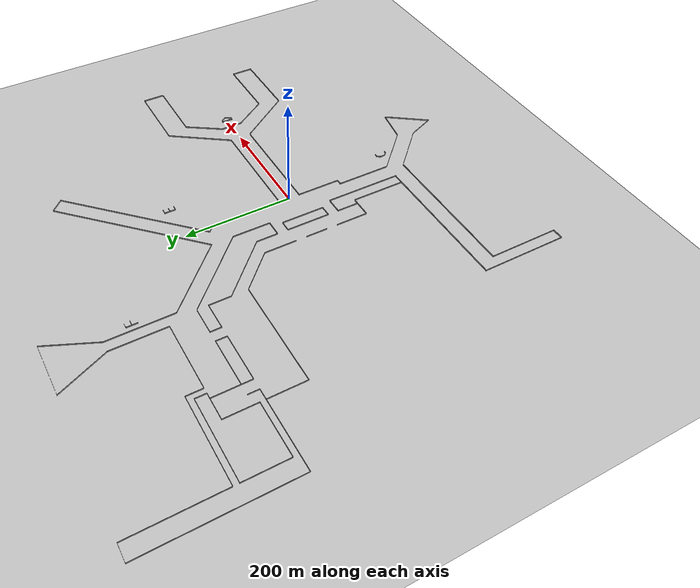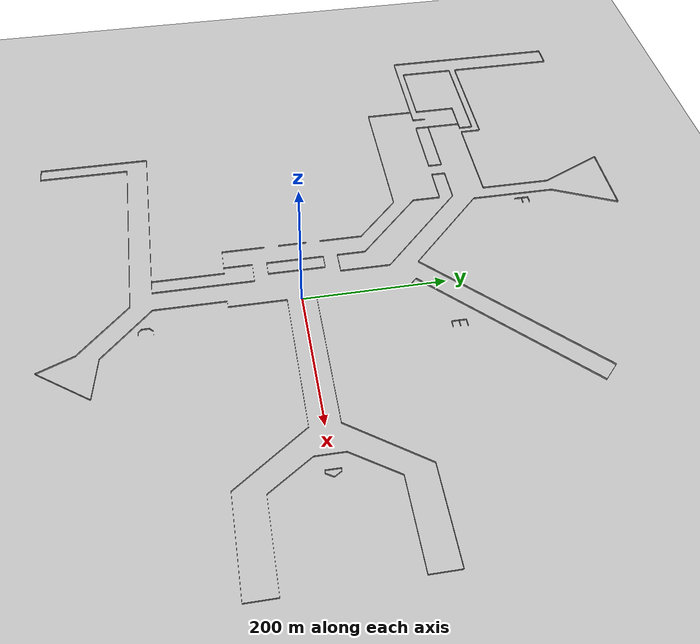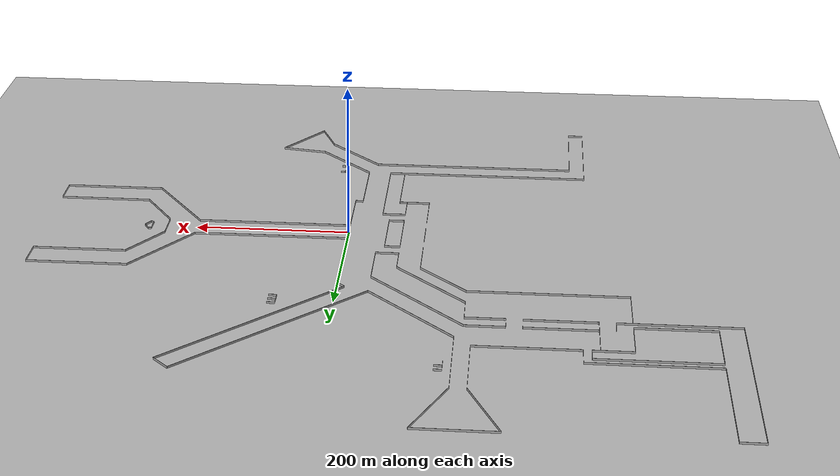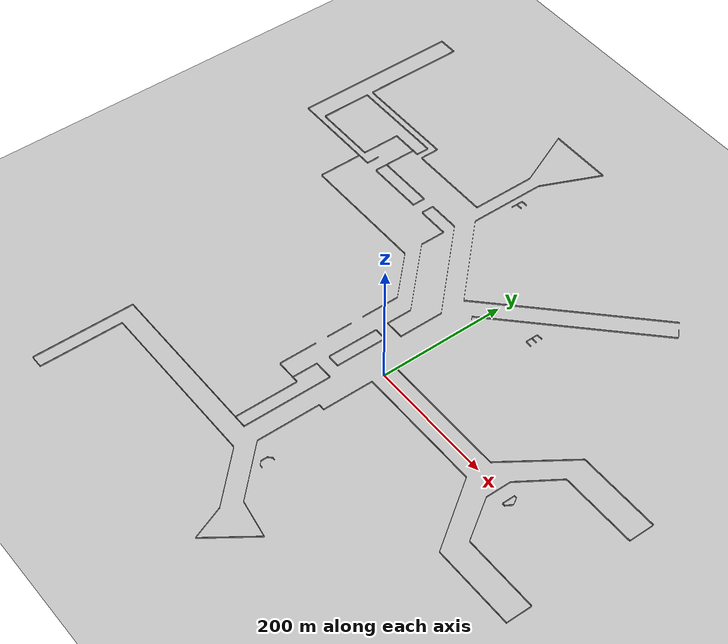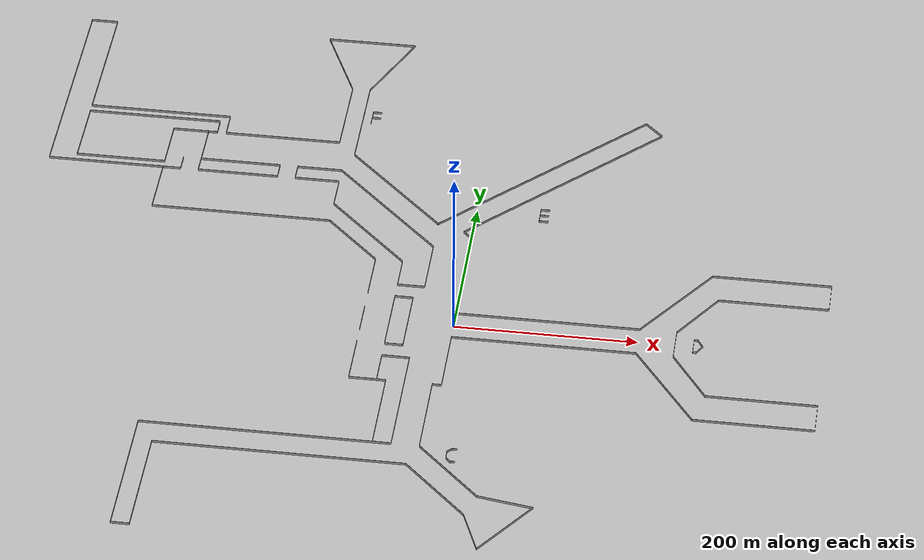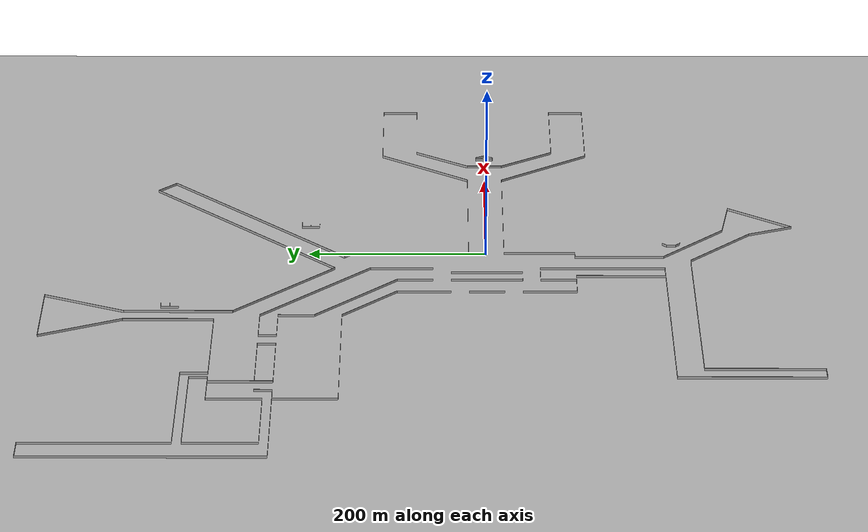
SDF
<?xml version="1.0" ?>

    <!-- this file is auto generated using pedsim_gazebo_plugin pkg -->
    <sdf version="1.5">
      <world name="default">

      <!-- Ground Plane -->

      <include>
        <uri>model://ground_plane</uri>
      </include>

      <include>
        <uri>model://sun</uri>
      </include>

     <model name='grey_wall_1'>
      <static>1</static>
      <link name='link'>

	  <pose frame=''>-155.0 -230.0  1.4 0 0 -0.0</pose>

        <collision name='collision'>
          <geometry>
            <box>

	     <size> 270.0 .2  2.8 </size>

      	   </box>
          </geometry>
          <max_contacts>10</max_contacts>
          <surface>
            <contact>
              <ode/>
            </contact>
            <bounce/>
            <friction>
              <torsional>
                <ode/>
              </torsional>
              <ode/>
            </friction>
          </surface>
        </collision>
        <visual name='visual'>
          <cast_shadows>0</cast_shadows>
          <geometry>
            <box>

	     <size> 270.0 .2  2.8 </size>

      	   </box>
       </geometry>
          <material>
            <script>
              <uri>model://grey_wall/materials/scripts</uri>
              <uri>model://grey_wall/materials/textures</uri>
              <name>vrc/grey_wall</name>
            </script>
          </material>
        </visual>
        <self_collide>0</self_collide>
        <enable_wind>0</enable_wind>
        <kinematic>0</kinematic>
      </link>
    </model>

     <model name='grey_wall_2'>
      <static>1</static>
      <link name='link'>

	  <pose frame=''>-175.0 -200.0  1.4 0 0 -0.0</pose>

        <collision name='collision'>
          <geometry>
            <box>

	     <size> 270.0 .2  2.8 </size>

      	   </box>
          </geometry>
          <max_contacts>10</max_contacts>
          <surface>
            <contact>
              <ode/>
            </contact>
            <bounce/>
            <friction>
              <torsional>
                <ode/>
              </torsional>
              <ode/>
            </friction>
          </surface>
        </collision>
        <visual name='visual'>
          <cast_shadows>0</cast_shadows>
          <geometry>
            <box>

	     <size> 270.0 .2  2.8 </size>

      	   </box>
       </geometry>
          <material>
            <script>
              <uri>model://grey_wall/materials/scripts</uri>
              <uri>model://grey_wall/materials/textures</uri>
              <name>vrc/grey_wall</name>
            </script>
          </material>
        </visual>
        <self_collide>0</self_collide>
        <enable_wind>0</enable_wind>
        <kinematic>0</kinematic>
      </link>
    </model>

     <model name='grey_wall_3'>
      <static>1</static>
      <link name='link'>

	  <pose frame=''>-80.0 -100.0  1.4 0 0 0.0</pose>

        <collision name='collision'>
          <geometry>
            <box>

	     <size> 40.0 .2  2.8 </size>

      	   </box>
          </geometry>
          <max_contacts>10</max_contacts>
          <surface>
            <contact>
              <ode/>
            </contact>
            <bounce/>
            <friction>
              <torsional>
                <ode/>
              </torsional>
              <ode/>
            </friction>
          </surface>
        </collision>
        <visual name='visual'>
          <cast_shadows>0</cast_shadows>
          <geometry>
            <box>

	     <size> 40.0 .2  2.8 </size>

      	   </box>
       </geometry>
          <material>
            <script>
              <uri>model://grey_wall/materials/scripts</uri>
              <uri>model://grey_wall/materials/textures</uri>
              <name>vrc/grey_wall</name>
            </script>
          </material>
        </visual>
        <self_collide>0</self_collide>
        <enable_wind>0</enable_wind>
        <kinematic>0</kinematic>
      </link>
    </model>

     <model name='grey_wall_4'>
      <static>1</static>
      <link name='link'>

	  <pose frame=''>-100.0 -70.0  1.4 0 0 1.57</pose>

        <collision name='collision'>
          <geometry>
            <box>

	     <size> 60.0 .2  2.8 </size>

      	   </box>
          </geometry>
          <max_contacts>10</max_contacts>
          <surface>
            <contact>
              <ode/>
            </contact>
            <bounce/>
            <friction>
              <torsional>
                <ode/>
              </torsional>
              <ode/>
            </friction>
          </surface>
        </collision>
        <visual name='visual'>
          <cast_shadows>0</cast_shadows>
          <geometry>
            <box>

	     <size> 60.0 .2  2.8 </size>

      	   </box>
       </geometry>
          <material>
            <script>
              <uri>model://grey_wall/materials/scripts</uri>
              <uri>model://grey_wall/materials/textures</uri>
              <name>vrc/grey_wall</name>
            </script>
          </material>
        </visual>
        <self_collide>0</self_collide>
        <enable_wind>0</enable_wind>
        <kinematic>0</kinematic>
      </link>
    </model>

     <model name='grey_wall_5'>
      <static>1</static>
      <link name='link'>

	  <pose frame=''>0.0 85.0  1.4 0 0 1.57</pose>

        <collision name='collision'>
          <geometry>
            <box>

	     <size> 130.0 .2  2.8 </size>

      	   </box>
          </geometry>
          <max_contacts>10</max_contacts>
          <surface>
            <contact>
              <ode/>
            </contact>
            <bounce/>
            <friction>
              <torsional>
                <ode/>
              </torsional>
              <ode/>
            </friction>
          </surface>
        </collision>
        <visual name='visual'>
          <cast_shadows>0</cast_shadows>
          <geometry>
            <box>

	     <size> 130.0 .2  2.8 </size>

      	   </box>
       </geometry>
          <material>
            <script>
              <uri>model://grey_wall/materials/scripts</uri>
              <uri>model://grey_wall/materials/textures</uri>
              <name>vrc/grey_wall</name>
            </script>
          </material>
        </visual>
        <self_collide>0</self_collide>
        <enable_wind>0</enable_wind>
        <kinematic>0</kinematic>
      </link>
    </model>

     <model name='grey_wall_6'>
      <static>1</static>
      <link name='link'>

	  <pose frame=''>-130.0 130.0  1.4 0 0 -0.785398163397</pose>

        <collision name='collision'>
          <geometry>
            <box>

	     <size> 84.8528137424 .2  2.8 </size>

      	   </box>
          </geometry>
          <max_contacts>10</max_contacts>
          <surface>
            <contact>
              <ode/>
            </contact>
            <bounce/>
            <friction>
              <torsional>
                <ode/>
              </torsional>
              <ode/>
            </friction>
          </surface>
        </collision>
        <visual name='visual'>
          <cast_shadows>0</cast_shadows>
          <geometry>
            <box>

	     <size> 84.8528137424 .2  2.8 </size>

      	   </box>
       </geometry>
          <material>
            <script>
              <uri>model://grey_wall/materials/scripts</uri>
              <uri>model://grey_wall/materials/textures</uri>
              <name>vrc/grey_wall</name>
            </script>
          </material>
        </visual>
        <self_collide>0</self_collide>
        <enable_wind>0</enable_wind>
        <kinematic>0</kinematic>
      </link>
    </model>

     <model name='grey_wall_7'>
      <static>1</static>
      <link name='link'>

	  <pose frame=''>100.0 -20.0  1.4 0 0 0.0</pose>

        <collision name='collision'>
          <geometry>
            <box>

	     <size> 200.0 .2  2.8 </size>

      	   </box>
          </geometry>
          <max_contacts>10</max_contacts>
          <surface>
            <contact>
              <ode/>
            </contact>
            <bounce/>
            <friction>
              <torsional>
                <ode/>
              </torsional>
              <ode/>
            </friction>
          </surface>
        </collision>
        <visual name='visual'>
          <cast_shadows>0</cast_shadows>
          <geometry>
            <box>

	     <size> 200.0 .2  2.8 </size>

      	   </box>
       </geometry>
          <material>
            <script>
              <uri>model://grey_wall/materials/scripts</uri>
              <uri>model://grey_wall/materials/textures</uri>
              <name>vrc/grey_wall</name>
            </script>
          </material>
        </visual>
        <self_collide>0</self_collide>
        <enable_wind>0</enable_wind>
        <kinematic>0</kinematic>
      </link>
    </model>

     <model name='grey_wall_8'>
      <static>1</static>
      <link name='link'>

	  <pose frame=''>100.0 20.0  1.4 0 0 0.0</pose>

        <collision name='collision'>
          <geometry>
            <box>

	     <size> 200.0 .2  2.8 </size>

      	   </box>
          </geometry>
          <max_contacts>10</max_contacts>
          <surface>
            <contact>
              <ode/>
            </contact>
            <bounce/>
            <friction>
              <torsional>
                <ode/>
              </torsional>
              <ode/>
            </friction>
          </surface>
        </collision>
        <visual name='visual'>
          <cast_shadows>0</cast_shadows>
          <geometry>
            <box>

	     <size> 200.0 .2  2.8 </size>

      	   </box>
       </geometry>
          <material>
            <script>
              <uri>model://grey_wall/materials/scripts</uri>
              <uri>model://grey_wall/materials/textures</uri>
              <name>vrc/grey_wall</name>
            </script>
          </material>
        </visual>
        <self_collide>0</self_collide>
        <enable_wind>0</enable_wind>
        <kinematic>0</kinematic>
      </link>
    </model>

     <model name='grey_wall_9'>
      <static>1</static>
      <link name='link'>

	  <pose frame=''>235.0 70.0  1.4 0 0 0.960070362406</pose>

        <collision name='collision'>
          <geometry>
            <box>

	     <size> 122.065556157 .2  2.8 </size>

      	   </box>
          </geometry>
          <max_contacts>10</max_contacts>
          <surface>
            <contact>
              <ode/>
            </contact>
            <bounce/>
            <friction>
              <torsional>
                <ode/>
              </torsional>
              <ode/>
            </friction>
          </surface>
        </collision>
        <visual name='visual'>
          <cast_shadows>0</cast_shadows>
          <geometry>
            <box>

	     <size> 122.065556157 .2  2.8 </size>

      	   </box>
       </geometry>
          <material>
            <script>
              <uri>model://grey_wall/materials/scripts</uri>
              <uri>model://grey_wall/materials/textures</uri>
              <name>vrc/grey_wall</name>
            </script>
          </material>
        </visual>
        <self_collide>0</self_collide>
        <enable_wind>0</enable_wind>
        <kinematic>0</kinematic>
      </link>
    </model>

     <model name='grey_wall_10'>
      <static>1</static>
      <link name='link'>

	  <pose frame=''>235.0 -70.0  1.4 0 0 -0.960070362406</pose>

        <collision name='collision'>
          <geometry>
            <box>

	     <size> 122.065556157 .2  2.8 </size>

      	   </box>
          </geometry>
          <max_contacts>10</max_contacts>
          <surface>
            <contact>
              <ode/>
            </contact>
            <bounce/>
            <friction>
              <torsional>
                <ode/>
              </torsional>
              <ode/>
            </friction>
          </surface>
        </collision>
        <visual name='visual'>
          <cast_shadows>0</cast_shadows>
          <geometry>
            <box>

	     <size> 122.065556157 .2  2.8 </size>

      	   </box>
       </geometry>
          <material>
            <script>
              <uri>model://grey_wall/materials/scripts</uri>
              <uri>model://grey_wall/materials/textures</uri>
              <name>vrc/grey_wall</name>
            </script>
          </material>
        </visual>
        <self_collide>0</self_collide>
        <enable_wind>0</enable_wind>
        <kinematic>0</kinematic>
      </link>
    </model>

     <model name='grey_wall_11'>
      <static>1</static>
      <link name='link'>

	  <pose frame=''>260.0 50.0  1.4 0 0 0.982793723247</pose>

        <collision name='collision'>
          <geometry>
            <box>

	     <size> 72.1110255093 .2  2.8 </size>

      	   </box>
          </geometry>
          <max_contacts>10</max_contacts>
          <surface>
            <contact>
              <ode/>
            </contact>
            <bounce/>
            <friction>
              <torsional>
                <ode/>
              </torsional>
              <ode/>
            </friction>
          </surface>
        </collision>
        <visual name='visual'>
          <cast_shadows>0</cast_shadows>
          <geometry>
            <box>

	     <size> 72.1110255093 .2  2.8 </size>

      	   </box>
       </geometry>
          <material>
            <script>
              <uri>model://grey_wall/materials/scripts</uri>
              <uri>model://grey_wall/materials/textures</uri>
              <name>vrc/grey_wall</name>
            </script>
          </material>
        </visual>
        <self_collide>0</self_collide>
        <enable_wind>0</enable_wind>
        <kinematic>0</kinematic>
      </link>
    </model>

     <model name='grey_wall_12'>
      <static>1</static>
      <link name='link'>

	  <pose frame=''>240.0 0.0  1.4 0 0 1.57</pose>

        <collision name='collision'>
          <geometry>
            <box>

	     <size> 40.0 .2  2.8 </size>

      	   </box>
          </geometry>
          <max_contacts>10</max_contacts>
          <surface>
            <contact>
              <ode/>
            </contact>
            <bounce/>
            <friction>
              <torsional>
                <ode/>
              </torsional>
              <ode/>
            </friction>
          </surface>
        </collision>
        <visual name='visual'>
          <cast_shadows>0</cast_shadows>
          <geometry>
            <box>

	     <size> 40.0 .2  2.8 </size>

      	   </box>
       </geometry>
          <material>
            <script>
              <uri>model://grey_wall/materials/scripts</uri>
              <uri>model://grey_wall/materials/textures</uri>
              <name>vrc/grey_wall</name>
            </script>
          </material>
        </visual>
        <self_collide>0</self_collide>
        <enable_wind>0</enable_wind>
        <kinematic>0</kinematic>
      </link>
    </model>

     <model name='grey_wall_13'>
      <static>1</static>
      <link name='link'>

	  <pose frame=''>260.0 -50.0  1.4 0 0 -0.982793723247</pose>

        <collision name='collision'>
          <geometry>
            <box>

	     <size> 72.1110255093 .2  2.8 </size>

      	   </box>
          </geometry>
          <max_contacts>10</max_contacts>
          <surface>
            <contact>
              <ode/>
            </contact>
            <bounce/>
            <friction>
              <torsional>
                <ode/>
              </torsional>
              <ode/>
            </friction>
          </surface>
        </collision>
        <visual name='visual'>
          <cast_shadows>0</cast_shadows>
          <geometry>
            <box>

	     <size> 72.1110255093 .2  2.8 </size>

      	   </box>
       </geometry>
          <material>
            <script>
              <uri>model://grey_wall/materials/scripts</uri>
              <uri>model://grey_wall/materials/textures</uri>
              <name>vrc/grey_wall</name>
            </script>
          </material>
        </visual>
        <self_collide>0</self_collide>
        <enable_wind>0</enable_wind>
        <kinematic>0</kinematic>
      </link>
    </model>

     <model name='grey_wall_14'>
      <static>1</static>
      <link name='link'>

	  <pose frame=''>0.0 -60.0  1.4 0 0 1.57</pose>

        <collision name='collision'>
          <geometry>
            <box>

	     <size> 80.0 .2  2.8 </size>

      	   </box>
          </geometry>
          <max_contacts>10</max_contacts>
          <surface>
            <contact>
              <ode/>
            </contact>
            <bounce/>
            <friction>
              <torsional>
                <ode/>
              </torsional>
              <ode/>
            </friction>
          </surface>
        </collision>
        <visual name='visual'>
          <cast_shadows>0</cast_shadows>
          <geometry>
            <box>

	     <size> 80.0 .2  2.8 </size>

      	   </box>
       </geometry>
          <material>
            <script>
              <uri>model://grey_wall/materials/scripts</uri>
              <uri>model://grey_wall/materials/textures</uri>
              <name>vrc/grey_wall</name>
            </script>
          </material>
        </visual>
        <self_collide>0</self_collide>
        <enable_wind>0</enable_wind>
        <kinematic>0</kinematic>
      </link>
    </model>

     <model name='grey_wall_15'>
      <static>1</static>
      <link name='link'>

	  <pose frame=''>340.0 80.0  1.4 0 0 0.0</pose>

        <collision name='collision'>
          <geometry>
            <box>

	     <size> 120.0 .2  2.8 </size>

      	   </box>
          </geometry>
          <max_contacts>10</max_contacts>
          <surface>
            <contact>
              <ode/>
            </contact>
            <bounce/>
            <friction>
              <torsional>
                <ode/>
              </torsional>
              <ode/>
            </friction>
          </surface>
        </collision>
        <visual name='visual'>
          <cast_shadows>0</cast_shadows>
          <geometry>
            <box>

	     <size> 120.0 .2  2.8 </size>

      	   </box>
       </geometry>
          <material>
            <script>
              <uri>model://grey_wall/materials/scripts</uri>
              <uri>model://grey_wall/materials/textures</uri>
              <name>vrc/grey_wall</name>
            </script>
          </material>
        </visual>
        <self_collide>0</self_collide>
        <enable_wind>0</enable_wind>
        <kinematic>0</kinematic>
      </link>
    </model>

     <model name='grey_wall_16'>
      <static>1</static>
      <link name='link'>

	  <pose frame=''>335.0 120.0  1.4 0 0 0.0</pose>

        <collision name='collision'>
          <geometry>
            <box>

	     <size> 130.0 .2  2.8 </size>

      	   </box>
          </geometry>
          <max_contacts>10</max_contacts>
          <surface>
            <contact>
              <ode/>
            </contact>
            <bounce/>
            <friction>
              <torsional>
                <ode/>
              </torsional>
              <ode/>
            </friction>
          </surface>
        </collision>
        <visual name='visual'>
          <cast_shadows>0</cast_shadows>
          <geometry>
            <box>

	     <size> 130.0 .2  2.8 </size>

      	   </box>
       </geometry>
          <material>
            <script>
              <uri>model://grey_wall/materials/scripts</uri>
              <uri>model://grey_wall/materials/textures</uri>
              <name>vrc/grey_wall</name>
            </script>
          </material>
        </visual>
        <self_collide>0</self_collide>
        <enable_wind>0</enable_wind>
        <kinematic>0</kinematic>
      </link>
    </model>

     <model name='grey_wall_17'>
      <static>1</static>
      <link name='link'>

	  <pose frame=''>340.0 -80.0  1.4 0 0 0.0</pose>

        <collision name='collision'>
          <geometry>
            <box>

	     <size> 120.0 .2  2.8 </size>

      	   </box>
          </geometry>
          <max_contacts>10</max_contacts>
          <surface>
            <contact>
              <ode/>
            </contact>
            <bounce/>
            <friction>
              <torsional>
                <ode/>
              </torsional>
              <ode/>
            </friction>
          </surface>
        </collision>
        <visual name='visual'>
          <cast_shadows>0</cast_shadows>
          <geometry>
            <box>

	     <size> 120.0 .2  2.8 </size>

      	   </box>
       </geometry>
          <material>
            <script>
              <uri>model://grey_wall/materials/scripts</uri>
              <uri>model://grey_wall/materials/textures</uri>
              <name>vrc/grey_wall</name>
            </script>
          </material>
        </visual>
        <self_collide>0</self_collide>
        <enable_wind>0</enable_wind>
        <kinematic>0</kinematic>
      </link>
    </model>

     <model name='grey_wall_18'>
      <static>1</static>
      <link name='link'>

	  <pose frame=''>335.0 -120.0  1.4 0 0 0.0</pose>

        <collision name='collision'>
          <geometry>
            <box>

	     <size> 130.0 .2  2.8 </size>

      	   </box>
          </geometry>
          <max_contacts>10</max_contacts>
          <surface>
            <contact>
              <ode/>
            </contact>
            <bounce/>
            <friction>
              <torsional>
                <ode/>
              </torsional>
              <ode/>
            </friction>
          </surface>
        </collision>
        <visual name='visual'>
          <cast_shadows>0</cast_shadows>
          <geometry>
            <box>

	     <size> 130.0 .2  2.8 </size>

      	   </box>
       </geometry>
          <material>
            <script>
              <uri>model://grey_wall/materials/scripts</uri>
              <uri>model://grey_wall/materials/textures</uri>
              <name>vrc/grey_wall</name>
            </script>
          </material>
        </visual>
        <self_collide>0</self_collide>
        <enable_wind>0</enable_wind>
        <kinematic>0</kinematic>
      </link>
    </model>

     <model name='grey_wall_19'>
      <static>1</static>
      <link name='link'>

	  <pose frame=''>-10.0 -150.0  1.4 0 0 1.57</pose>

        <collision name='collision'>
          <geometry>
            <box>

	     <size> 100.0 .2  2.8 </size>

      	   </box>
          </geometry>
          <max_contacts>10</max_contacts>
          <surface>
            <contact>
              <ode/>
            </contact>
            <bounce/>
            <friction>
              <torsional>
                <ode/>
              </torsional>
              <ode/>
            </friction>
          </surface>
        </collision>
        <visual name='visual'>
          <cast_shadows>0</cast_shadows>
          <geometry>
            <box>

	     <size> 100.0 .2  2.8 </size>

      	   </box>
       </geometry>
          <material>
            <script>
              <uri>model://grey_wall/materials/scripts</uri>
              <uri>model://grey_wall/materials/textures</uri>
              <name>vrc/grey_wall</name>
            </script>
          </material>
        </visual>
        <self_collide>0</self_collide>
        <enable_wind>0</enable_wind>
        <kinematic>0</kinematic>
      </link>
    </model>

     <model name='grey_wall_20'>
      <static>1</static>
      <link name='link'>

	  <pose frame=''>-60.0 -150.0  1.4 0 0 1.57</pose>

        <collision name='collision'>
          <geometry>
            <box>

	     <size> 100.0 .2  2.8 </size>

      	   </box>
          </geometry>
          <max_contacts>10</max_contacts>
          <surface>
            <contact>
              <ode/>
            </contact>
            <bounce/>
            <friction>
              <torsional>
                <ode/>
              </torsional>
              <ode/>
            </friction>
          </surface>
        </collision>
        <visual name='visual'>
          <cast_shadows>0</cast_shadows>
          <geometry>
            <box>

	     <size> 100.0 .2  2.8 </size>

      	   </box>
       </geometry>
          <material>
            <script>
              <uri>model://grey_wall/materials/scripts</uri>
              <uri>model://grey_wall/materials/textures</uri>
              <name>vrc/grey_wall</name>
            </script>
          </material>
        </visual>
        <self_collide>0</self_collide>
        <enable_wind>0</enable_wind>
        <kinematic>0</kinematic>
      </link>
    </model>

     <model name='grey_wall_21'>
      <static>1</static>
      <link name='link'>

	  <pose frame=''>400.0 100.0  1.4 0 0 1.57</pose>

        <collision name='collision'>
          <geometry>
            <box>

	     <size> 40.0 .2  2.8 </size>

      	   </box>
          </geometry>
          <max_contacts>10</max_contacts>
          <surface>
            <contact>
              <ode/>
            </contact>
            <bounce/>
            <friction>
              <torsional>
                <ode/>
              </torsional>
              <ode/>
            </friction>
          </surface>
        </collision>
        <visual name='visual'>
          <cast_shadows>0</cast_shadows>
          <geometry>
            <box>

	     <size> 40.0 .2  2.8 </size>

      	   </box>
       </geometry>
          <material>
            <script>
              <uri>model://grey_wall/materials/scripts</uri>
              <uri>model://grey_wall/materials/textures</uri>
              <name>vrc/grey_wall</name>
            </script>
          </material>
        </visual>
        <self_collide>0</self_collide>
        <enable_wind>0</enable_wind>
        <kinematic>0</kinematic>
      </link>
    </model>

     <model name='grey_wall_22'>
      <static>1</static>
      <link name='link'>

	  <pose frame=''>400.0 -100.0  1.4 0 0 1.57</pose>

        <collision name='collision'>
          <geometry>
            <box>

	     <size> 40.0 .2  2.8 </size>

      	   </box>
          </geometry>
          <max_contacts>10</max_contacts>
          <surface>
            <contact>
              <ode/>
            </contact>
            <bounce/>
            <friction>
              <torsional>
                <ode/>
              </torsional>
              <ode/>
            </friction>
          </surface>
        </collision>
        <visual name='visual'>
          <cast_shadows>0</cast_shadows>
          <geometry>
            <box>

	     <size> 40.0 .2  2.8 </size>

      	   </box>
       </geometry>
          <material>
            <script>
              <uri>model://grey_wall/materials/scripts</uri>
              <uri>model://grey_wall/materials/textures</uri>
              <name>vrc/grey_wall</name>
            </script>
          </material>
        </visual>
        <self_collide>0</self_collide>
        <enable_wind>0</enable_wind>
        <kinematic>0</kinematic>
      </link>
    </model>

     <model name='grey_wall_23'>
      <static>1</static>
      <link name='link'>

	  <pose frame=''>-260.0 160.0  1.4 0 0 -0.0</pose>

        <collision name='collision'>
          <geometry>
            <box>

	     <size> 200.0 .2  2.8 </size>

      	   </box>
          </geometry>
          <max_contacts>10</max_contacts>
          <surface>
            <contact>
              <ode/>
            </contact>
            <bounce/>
            <friction>
              <torsional>
                <ode/>
              </torsional>
              <ode/>
            </friction>
          </surface>
        </collision>
        <visual name='visual'>
          <cast_shadows>0</cast_shadows>
          <geometry>
            <box>

	     <size> 200.0 .2  2.8 </size>

      	   </box>
       </geometry>
          <material>
            <script>
              <uri>model://grey_wall/materials/scripts</uri>
              <uri>model://grey_wall/materials/textures</uri>
              <name>vrc/grey_wall</name>
            </script>
          </material>
        </visual>
        <self_collide>0</self_collide>
        <enable_wind>0</enable_wind>
        <kinematic>0</kinematic>
      </link>
    </model>

     <model name='grey_wall_24'>
      <static>1</static>
      <link name='link'>

	  <pose frame=''>-5.0 -100.0  1.4 0 0 0.0</pose>

        <collision name='collision'>
          <geometry>
            <box>

	     <size> 10.0 .2  2.8 </size>

      	   </box>
          </geometry>
          <max_contacts>10</max_contacts>
          <surface>
            <contact>
              <ode/>
            </contact>
            <bounce/>
            <friction>
              <torsional>
                <ode/>
              </torsional>
              <ode/>
            </friction>
          </surface>
        </collision>
        <visual name='visual'>
          <cast_shadows>0</cast_shadows>
          <geometry>
            <box>

	     <size> 10.0 .2  2.8 </size>

      	   </box>
       </geometry>
          <material>
            <script>
              <uri>model://grey_wall/materials/scripts</uri>
              <uri>model://grey_wall/materials/textures</uri>
              <name>vrc/grey_wall</name>
            </script>
          </material>
        </visual>
        <self_collide>0</self_collide>
        <enable_wind>0</enable_wind>
        <kinematic>0</kinematic>
      </link>
    </model>

     <model name='grey_wall_25'>
      <static>1</static>
      <link name='link'>

	  <pose frame=''>25.0 -235.0  1.4 0 0 -0.785398163397</pose>

        <collision name='collision'>
          <geometry>
            <box>

	     <size> 98.9949493661 .2  2.8 </size>

      	   </box>
          </geometry>
          <max_contacts>10</max_contacts>
          <surface>
            <contact>
              <ode/>
            </contact>
            <bounce/>
            <friction>
              <torsional>
                <ode/>
              </torsional>
              <ode/>
            </friction>
          </surface>
        </collision>
        <visual name='visual'>
          <cast_shadows>0</cast_shadows>
          <geometry>
            <box>

	     <size> 98.9949493661 .2  2.8 </size>

      	   </box>
       </geometry>
          <material>
            <script>
              <uri>model://grey_wall/materials/scripts</uri>
              <uri>model://grey_wall/materials/textures</uri>
              <name>vrc/grey_wall</name>
            </script>
          </material>
        </visual>
        <self_collide>0</self_collide>
        <enable_wind>0</enable_wind>
        <kinematic>0</kinematic>
      </link>
    </model>

     <model name='grey_wall_26'>
      <static>1</static>
      <link name='link'>

	  <pose frame=''>15.0 -265.0  1.4 0 0 -0.785398163397</pose>

        <collision name='collision'>
          <geometry>
            <box>

	     <size> 98.9949493661 .2  2.8 </size>

      	   </box>
          </geometry>
          <max_contacts>10</max_contacts>
          <surface>
            <contact>
              <ode/>
            </contact>
            <bounce/>
            <friction>
              <torsional>
                <ode/>
              </torsional>
              <ode/>
            </friction>
          </surface>
        </collision>
        <visual name='visual'>
          <cast_shadows>0</cast_shadows>
          <geometry>
            <box>

	     <size> 98.9949493661 .2  2.8 </size>

      	   </box>
       </geometry>
          <material>
            <script>
              <uri>model://grey_wall/materials/scripts</uri>
              <uri>model://grey_wall/materials/textures</uri>
              <name>vrc/grey_wall</name>
            </script>
          </material>
        </visual>
        <self_collide>0</self_collide>
        <enable_wind>0</enable_wind>
        <kinematic>0</kinematic>
      </link>
    </model>

     <model name='grey_wall_27'>
      <static>1</static>
      <link name='link'>

	  <pose frame=''>90.0 -275.0  1.4 0 0 -0.165148677415</pose>

        <collision name='collision'>
          <geometry>
            <box>

	     <size> 60.827625303 .2  2.8 </size>

      	   </box>
          </geometry>
          <max_contacts>10</max_contacts>
          <surface>
            <contact>
              <ode/>
            </contact>
            <bounce/>
            <friction>
              <torsional>
                <ode/>
              </torsional>
              <ode/>
            </friction>
          </surface>
        </collision>
        <visual name='visual'>
          <cast_shadows>0</cast_shadows>
          <geometry>
            <box>

	     <size> 60.827625303 .2  2.8 </size>

      	   </box>
       </geometry>
          <material>
            <script>
              <uri>model://grey_wall/materials/scripts</uri>
              <uri>model://grey_wall/materials/textures</uri>
              <name>vrc/grey_wall</name>
            </script>
          </material>
        </visual>
        <self_collide>0</self_collide>
        <enable_wind>0</enable_wind>
        <kinematic>0</kinematic>
      </link>
    </model>

     <model name='grey_wall_28'>
      <static>1</static>
      <link name='link'>

	  <pose frame=''>60.0 -325.0  1.4 0 0 -1.19028994968</pose>

        <collision name='collision'>
          <geometry>
            <box>

	     <size> 53.8516480713 .2  2.8 </size>

      	   </box>
          </geometry>
          <max_contacts>10</max_contacts>
          <surface>
            <contact>
              <ode/>
            </contact>
            <bounce/>
            <friction>
              <torsional>
                <ode/>
              </torsional>
              <ode/>
            </friction>
          </surface>
        </collision>
        <visual name='visual'>
          <cast_shadows>0</cast_shadows>
          <geometry>
            <box>

	     <size> 53.8516480713 .2  2.8 </size>

      	   </box>
       </geometry>
          <material>
            <script>
              <uri>model://grey_wall/materials/scripts</uri>
              <uri>model://grey_wall/materials/textures</uri>
              <name>vrc/grey_wall</name>
            </script>
          </material>
        </visual>
        <self_collide>0</self_collide>
        <enable_wind>0</enable_wind>
        <kinematic>0</kinematic>
      </link>
    </model>

     <model name='grey_wall_29'>
      <static>1</static>
      <link name='link'>

	  <pose frame=''>95.0 -315.0  1.4 0 0 0.950546840812</pose>

        <collision name='collision'>
          <geometry>
            <box>

	     <size> 86.0232526704 .2  2.8 </size>

      	   </box>
          </geometry>
          <max_contacts>10</max_contacts>
          <surface>
            <contact>
              <ode/>
            </contact>
            <bounce/>
            <friction>
              <torsional>
                <ode/>
              </torsional>
              <ode/>
            </friction>
          </surface>
        </collision>
        <visual name='visual'>
          <cast_shadows>0</cast_shadows>
          <geometry>
            <box>

	     <size> 86.0232526704 .2  2.8 </size>

      	   </box>
       </geometry>
          <material>
            <script>
              <uri>model://grey_wall/materials/scripts</uri>
              <uri>model://grey_wall/materials/textures</uri>
              <name>vrc/grey_wall</name>
            </script>
          </material>
        </visual>
        <self_collide>0</self_collide>
        <enable_wind>0</enable_wind>
        <kinematic>0</kinematic>
      </link>
    </model>

     <model name='grey_wall_30'>
      <static>1</static>
      <link name='link'>

	  <pose frame=''>-290.0 -295.0  1.4 0 0 1.57</pose>

        <collision name='collision'>
          <geometry>
            <box>

	     <size> 130.0 .2  2.8 </size>

      	   </box>
          </geometry>
          <max_contacts>10</max_contacts>
          <surface>
            <contact>
              <ode/>
            </contact>
            <bounce/>
            <friction>
              <torsional>
                <ode/>
              </torsional>
              <ode/>
            </friction>
          </surface>
        </collision>
        <visual name='visual'>
          <cast_shadows>0</cast_shadows>
          <geometry>
            <box>

	     <size> 130.0 .2  2.8 </size>

      	   </box>
       </geometry>
          <material>
            <script>
              <uri>model://grey_wall/materials/scripts</uri>
              <uri>model://grey_wall/materials/textures</uri>
              <name>vrc/grey_wall</name>
            </script>
          </material>
        </visual>
        <self_collide>0</self_collide>
        <enable_wind>0</enable_wind>
        <kinematic>0</kinematic>
      </link>
    </model>

     <model name='grey_wall_31'>
      <static>1</static>
      <link name='link'>

	  <pose frame=''>-310.0 -280.0  1.4 0 0 1.57</pose>

        <collision name='collision'>
          <geometry>
            <box>

	     <size> 160.0 .2  2.8 </size>

      	   </box>
          </geometry>
          <max_contacts>10</max_contacts>
          <surface>
            <contact>
              <ode/>
            </contact>
            <bounce/>
            <friction>
              <torsional>
                <ode/>
              </torsional>
              <ode/>
            </friction>
          </surface>
        </collision>
        <visual name='visual'>
          <cast_shadows>0</cast_shadows>
          <geometry>
            <box>

	     <size> 160.0 .2  2.8 </size>

      	   </box>
       </geometry>
          <material>
            <script>
              <uri>model://grey_wall/materials/scripts</uri>
              <uri>model://grey_wall/materials/textures</uri>
              <name>vrc/grey_wall</name>
            </script>
          </material>
        </visual>
        <self_collide>0</self_collide>
        <enable_wind>0</enable_wind>
        <kinematic>0</kinematic>
      </link>
    </model>

     <model name='grey_wall_32'>
      <static>1</static>
      <link name='link'>

	  <pose frame=''>-300.0 -360.0  1.4 0 0 0.0</pose>

        <collision name='collision'>
          <geometry>
            <box>

	     <size> 20.0 .2  2.8 </size>

      	   </box>
          </geometry>
          <max_contacts>10</max_contacts>
          <surface>
            <contact>
              <ode/>
            </contact>
            <bounce/>
            <friction>
              <torsional>
                <ode/>
              </torsional>
              <ode/>
            </friction>
          </surface>
        </collision>
        <visual name='visual'>
          <cast_shadows>0</cast_shadows>
          <geometry>
            <box>

	     <size> 20.0 .2  2.8 </size>

      	   </box>
       </geometry>
          <material>
            <script>
              <uri>model://grey_wall/materials/scripts</uri>
              <uri>model://grey_wall/materials/textures</uri>
              <name>vrc/grey_wall</name>
            </script>
          </material>
        </visual>
        <self_collide>0</self_collide>
        <enable_wind>0</enable_wind>
        <kinematic>0</kinematic>
      </link>
    </model>

     <model name='grey_wall_33'>
      <static>1</static>
      <link name='link'>

	  <pose frame=''>90.0 260.0  1.4 0 0 0.785398163397</pose>

        <collision name='collision'>
          <geometry>
            <box>

	     <size> 282.842712475 .2  2.8 </size>

      	   </box>
          </geometry>
          <max_contacts>10</max_contacts>
          <surface>
            <contact>
              <ode/>
            </contact>
            <bounce/>
            <friction>
              <torsional>
                <ode/>
              </torsional>
              <ode/>
            </friction>
          </surface>
        </collision>
        <visual name='visual'>
          <cast_shadows>0</cast_shadows>
          <geometry>
            <box>

	     <size> 282.842712475 .2  2.8 </size>

      	   </box>
       </geometry>
          <material>
            <script>
              <uri>model://grey_wall/materials/scripts</uri>
              <uri>model://grey_wall/materials/textures</uri>
              <name>vrc/grey_wall</name>
            </script>
          </material>
        </visual>
        <self_collide>0</self_collide>
        <enable_wind>0</enable_wind>
        <kinematic>0</kinematic>
      </link>
    </model>

     <model name='grey_wall_34'>
      <static>1</static>
      <link name='link'>

	  <pose frame=''>65.0 275.0  1.4 0 0 0.785398163397</pose>

        <collision name='collision'>
          <geometry>
            <box>

	     <size> 296.984848098 .2  2.8 </size>

      	   </box>
          </geometry>
          <max_contacts>10</max_contacts>
          <surface>
            <contact>
              <ode/>
            </contact>
            <bounce/>
            <friction>
              <torsional>
                <ode/>
              </torsional>
              <ode/>
            </friction>
          </surface>
        </collision>
        <visual name='visual'>
          <cast_shadows>0</cast_shadows>
          <geometry>
            <box>

	     <size> 296.984848098 .2  2.8 </size>

      	   </box>
       </geometry>
          <material>
            <script>
              <uri>model://grey_wall/materials/scripts</uri>
              <uri>model://grey_wall/materials/textures</uri>
              <name>vrc/grey_wall</name>
            </script>
          </material>
        </visual>
        <self_collide>0</self_collide>
        <enable_wind>0</enable_wind>
        <kinematic>0</kinematic>
      </link>
    </model>

     <model name='grey_wall_35'>
      <static>1</static>
      <link name='link'>

	  <pose frame=''>180.0 370.0  1.4 0 0 -0.785398163397</pose>

        <collision name='collision'>
          <geometry>
            <box>

	     <size> 28.2842712475 .2  2.8 </size>

      	   </box>
          </geometry>
          <max_contacts>10</max_contacts>
          <surface>
            <contact>
              <ode/>
            </contact>
            <bounce/>
            <friction>
              <torsional>
                <ode/>
              </torsional>
              <ode/>
            </friction>
          </surface>
        </collision>
        <visual name='visual'>
          <cast_shadows>0</cast_shadows>
          <geometry>
            <box>

	     <size> 28.2842712475 .2  2.8 </size>

      	   </box>
       </geometry>
          <material>
            <script>
              <uri>model://grey_wall/materials/scripts</uri>
              <uri>model://grey_wall/materials/textures</uri>
              <name>vrc/grey_wall</name>
            </script>
          </material>
        </visual>
        <self_collide>0</self_collide>
        <enable_wind>0</enable_wind>
        <kinematic>0</kinematic>
      </link>
    </model>

     <model name='grey_wall_36'>
      <static>1</static>
      <link name='link'>

	  <pose frame=''>-170.0 350.0  1.4 0 0 1.57</pose>

        <collision name='collision'>
          <geometry>
            <box>

	     <size> 100.0 .2  2.8 </size>

      	   </box>
          </geometry>
          <max_contacts>10</max_contacts>
          <surface>
            <contact>
              <ode/>
            </contact>
            <bounce/>
            <friction>
              <torsional>
                <ode/>
              </torsional>
              <ode/>
            </friction>
          </surface>
        </collision>
        <visual name='visual'>
          <cast_shadows>0</cast_shadows>
          <geometry>
            <box>

	     <size> 100.0 .2  2.8 </size>

      	   </box>
       </geometry>
          <material>
            <script>
              <uri>model://grey_wall/materials/scripts</uri>
              <uri>model://grey_wall/materials/textures</uri>
              <name>vrc/grey_wall</name>
            </script>
          </material>
        </visual>
        <self_collide>0</self_collide>
        <enable_wind>0</enable_wind>
        <kinematic>0</kinematic>
      </link>
    </model>

     <model name='grey_wall_37'>
      <static>1</static>
      <link name='link'>

	  <pose frame=''>-95.0 225.0  1.4 0 0 -0.785398163397</pose>

        <collision name='collision'>
          <geometry>
            <box>

	     <size> 155.563491861 .2  2.8 </size>

      	   </box>
          </geometry>
          <max_contacts>10</max_contacts>
          <surface>
            <contact>
              <ode/>
            </contact>
            <bounce/>
            <friction>
              <torsional>
                <ode/>
              </torsional>
              <ode/>
            </friction>
          </surface>
        </collision>
        <visual name='visual'>
          <cast_shadows>0</cast_shadows>
          <geometry>
            <box>

	     <size> 155.563491861 .2  2.8 </size>

      	   </box>
       </geometry>
          <material>
            <script>
              <uri>model://grey_wall/materials/scripts</uri>
              <uri>model://grey_wall/materials/textures</uri>
              <name>vrc/grey_wall</name>
            </script>
          </material>
        </visual>
        <self_collide>0</self_collide>
        <enable_wind>0</enable_wind>
        <kinematic>0</kinematic>
      </link>
    </model>

     <model name='grey_wall_38'>
      <static>1</static>
      <link name='link'>

	  <pose frame=''>-360.0 195.0  1.4 0 0 1.57</pose>

        <collision name='collision'>
          <geometry>
            <box>

	     <size> 70.0 .2  2.8 </size>

      	   </box>
          </geometry>
          <max_contacts>10</max_contacts>
          <surface>
            <contact>
              <ode/>
            </contact>
            <bounce/>
            <friction>
              <torsional>
                <ode/>
              </torsional>
              <ode/>
            </friction>
          </surface>
        </collision>
        <visual name='visual'>
          <cast_shadows>0</cast_shadows>
          <geometry>
            <box>

	     <size> 70.0 .2  2.8 </size>

      	   </box>
       </geometry>
          <material>
            <script>
              <uri>model://grey_wall/materials/scripts</uri>
              <uri>model://grey_wall/materials/textures</uri>
              <name>vrc/grey_wall</name>
            </script>
          </material>
        </visual>
        <self_collide>0</self_collide>
        <enable_wind>0</enable_wind>
        <kinematic>0</kinematic>
      </link>
    </model>

     <model name='grey_wall_39'>
      <static>1</static>
      <link name='link'>

	  <pose frame=''>-335.0 300.0  1.4 0 0 0.0</pose>

        <collision name='collision'>
          <geometry>
            <box>

	     <size> 50.0 .2  2.8 </size>

      	   </box>
          </geometry>
          <max_contacts>10</max_contacts>
          <surface>
            <contact>
              <ode/>
            </contact>
            <bounce/>
            <friction>
              <torsional>
                <ode/>
              </torsional>
              <ode/>
            </friction>
          </surface>
        </collision>
        <visual name='visual'>
          <cast_shadows>0</cast_shadows>
          <geometry>
            <box>

	     <size> 50.0 .2  2.8 </size>

      	   </box>
       </geometry>
          <material>
            <script>
              <uri>model://grey_wall/materials/scripts</uri>
              <uri>model://grey_wall/materials/textures</uri>
              <name>vrc/grey_wall</name>
            </script>
          </material>
        </visual>
        <self_collide>0</self_collide>
        <enable_wind>0</enable_wind>
        <kinematic>0</kinematic>
      </link>
    </model>

     <model name='grey_wall_40'>
      <static>1</static>
      <link name='link'>

	  <pose frame=''>-150.0 340.0  1.4 0 0 1.57</pose>

        <collision name='collision'>
          <geometry>
            <box>

	     <size> 120.0 .2  2.8 </size>

      	   </box>
          </geometry>
          <max_contacts>10</max_contacts>
          <surface>
            <contact>
              <ode/>
            </contact>
            <bounce/>
            <friction>
              <torsional>
                <ode/>
              </torsional>
              <ode/>
            </friction>
          </surface>
        </collision>
        <visual name='visual'>
          <cast_shadows>0</cast_shadows>
          <geometry>
            <box>

	     <size> 120.0 .2  2.8 </size>

      	   </box>
       </geometry>
          <material>
            <script>
              <uri>model://grey_wall/materials/scripts</uri>
              <uri>model://grey_wall/materials/textures</uri>
              <name>vrc/grey_wall</name>
            </script>
          </material>
        </visual>
        <self_collide>0</self_collide>
        <enable_wind>0</enable_wind>
        <kinematic>0</kinematic>
      </link>
    </model>

     <model name='grey_wall_41'>
      <static>1</static>
      <link name='link'>

	  <pose frame=''>-190.0 445.0  1.4 0 0 -1.15257199722</pose>

        <collision name='collision'>
          <geometry>
            <box>

	     <size> 98.488578018 .2  2.8 </size>

      	   </box>
          </geometry>
          <max_contacts>10</max_contacts>
          <surface>
            <contact>
              <ode/>
            </contact>
            <bounce/>
            <friction>
              <torsional>
                <ode/>
              </torsional>
              <ode/>
            </friction>
          </surface>
        </collision>
        <visual name='visual'>
          <cast_shadows>0</cast_shadows>
          <geometry>
            <box>

	     <size> 98.488578018 .2  2.8 </size>

      	   </box>
       </geometry>
          <material>
            <script>
              <uri>model://grey_wall/materials/scripts</uri>
              <uri>model://grey_wall/materials/textures</uri>
              <name>vrc/grey_wall</name>
            </script>
          </material>
        </visual>
        <self_collide>0</self_collide>
        <enable_wind>0</enable_wind>
        <kinematic>0</kinematic>
      </link>
    </model>

     <model name='grey_wall_42'>
      <static>1</static>
      <link name='link'>

	  <pose frame=''>-130.0 445.0  1.4 0 0 1.15257199722</pose>

        <collision name='collision'>
          <geometry>
            <box>

	     <size> 98.488578018 .2  2.8 </size>

      	   </box>
          </geometry>
          <max_contacts>10</max_contacts>
          <surface>
            <contact>
              <ode/>
            </contact>
            <bounce/>
            <friction>
              <torsional>
                <ode/>
              </torsional>
              <ode/>
            </friction>
          </surface>
        </collision>
        <visual name='visual'>
          <cast_shadows>0</cast_shadows>
          <geometry>
            <box>

	     <size> 98.488578018 .2  2.8 </size>

      	   </box>
       </geometry>
          <material>
            <script>
              <uri>model://grey_wall/materials/scripts</uri>
              <uri>model://grey_wall/materials/textures</uri>
              <name>vrc/grey_wall</name>
            </script>
          </material>
        </visual>
        <self_collide>0</self_collide>
        <enable_wind>0</enable_wind>
        <kinematic>0</kinematic>
      </link>
    </model>

     <model name='grey_wall_43'>
      <static>1</static>
      <link name='link'>

	  <pose frame=''>-160.0 490.0  1.4 0 0 0.0</pose>

        <collision name='collision'>
          <geometry>
            <box>

	     <size> 100.0 .2  2.8 </size>

      	   </box>
          </geometry>
          <max_contacts>10</max_contacts>
          <surface>
            <contact>
              <ode/>
            </contact>
            <bounce/>
            <friction>
              <torsional>
                <ode/>
              </torsional>
              <ode/>
            </friction>
          </surface>
        </collision>
        <visual name='visual'>
          <cast_shadows>0</cast_shadows>
          <geometry>
            <box>

	     <size> 100.0 .2  2.8 </size>

      	   </box>
       </geometry>
          <material>
            <script>
              <uri>model://grey_wall/materials/scripts</uri>
              <uri>model://grey_wall/materials/textures</uri>
              <name>vrc/grey_wall</name>
            </script>
          </material>
        </visual>
        <self_collide>0</self_collide>
        <enable_wind>0</enable_wind>
        <kinematic>0</kinematic>
      </link>
    </model>

     <model name='grey_wall_44'>
      <static>1</static>
      <link name='link'>

	  <pose frame=''>-415.0 230.0  1.4 0 0 -0.0</pose>

        <collision name='collision'>
          <geometry>
            <box>

	     <size> 150.0 .2  2.8 </size>

      	   </box>
          </geometry>
          <max_contacts>10</max_contacts>
          <surface>
            <contact>
              <ode/>
            </contact>
            <bounce/>
            <friction>
              <torsional>
                <ode/>
              </torsional>
              <ode/>
            </friction>
          </surface>
        </collision>
        <visual name='visual'>
          <cast_shadows>0</cast_shadows>
          <geometry>
            <box>

	     <size> 150.0 .2  2.8 </size>

      	   </box>
       </geometry>
          <material>
            <script>
              <uri>model://grey_wall/materials/scripts</uri>
              <uri>model://grey_wall/materials/textures</uri>
              <name>vrc/grey_wall</name>
            </script>
          </material>
        </visual>
        <self_collide>0</self_collide>
        <enable_wind>0</enable_wind>
        <kinematic>0</kinematic>
      </link>
    </model>

     <model name='grey_wall_45'>
      <static>1</static>
      <link name='link'>

	  <pose frame=''>-360.0 270.0  1.4 0 0 1.57</pose>

        <collision name='collision'>
          <geometry>
            <box>

	     <size> 60.0 .2  2.8 </size>

      	   </box>
          </geometry>
          <max_contacts>10</max_contacts>
          <surface>
            <contact>
              <ode/>
            </contact>
            <bounce/>
            <friction>
              <torsional>
                <ode/>
              </torsional>
              <ode/>
            </friction>
          </surface>
        </collision>
        <visual name='visual'>
          <cast_shadows>0</cast_shadows>
          <geometry>
            <box>

	     <size> 60.0 .2  2.8 </size>

      	   </box>
       </geometry>
          <material>
            <script>
              <uri>model://grey_wall/materials/scripts</uri>
              <uri>model://grey_wall/materials/textures</uri>
              <name>vrc/grey_wall</name>
            </script>
          </material>
        </visual>
        <self_collide>0</self_collide>
        <enable_wind>0</enable_wind>
        <kinematic>0</kinematic>
      </link>
    </model>

     <model name='grey_wall_46'>
      <static>1</static>
      <link name='link'>

	  <pose frame=''>-410.0 240.0  1.4 0 0 -0.0</pose>

        <collision name='collision'>
          <geometry>
            <box>

	     <size> 100.0 .2  2.8 </size>

      	   </box>
          </geometry>
          <max_contacts>10</max_contacts>
          <surface>
            <contact>
              <ode/>
            </contact>
            <bounce/>
            <friction>
              <torsional>
                <ode/>
              </torsional>
              <ode/>
            </friction>
          </surface>
        </collision>
        <visual name='visual'>
          <cast_shadows>0</cast_shadows>
          <geometry>
            <box>

	     <size> 100.0 .2  2.8 </size>

      	   </box>
       </geometry>
          <material>
            <script>
              <uri>model://grey_wall/materials/scripts</uri>
              <uri>model://grey_wall/materials/textures</uri>
              <name>vrc/grey_wall</name>
            </script>
          </material>
        </visual>
        <self_collide>0</self_collide>
        <enable_wind>0</enable_wind>
        <kinematic>0</kinematic>
      </link>
    </model>

     <model name='grey_wall_47'>
      <static>1</static>
      <link name='link'>

	  <pose frame=''>-460.0 280.0  1.4 0 0 1.57</pose>

        <collision name='collision'>
          <geometry>
            <box>

	     <size> 80.0 .2  2.8 </size>

      	   </box>
          </geometry>
          <max_contacts>10</max_contacts>
          <surface>
            <contact>
              <ode/>
            </contact>
            <bounce/>
            <friction>
              <torsional>
                <ode/>
              </torsional>
              <ode/>
            </friction>
          </surface>
        </collision>
        <visual name='visual'>
          <cast_shadows>0</cast_shadows>
          <geometry>
            <box>

	     <size> 80.0 .2  2.8 </size>

      	   </box>
       </geometry>
          <material>
            <script>
              <uri>model://grey_wall/materials/scripts</uri>
              <uri>model://grey_wall/materials/textures</uri>
              <name>vrc/grey_wall</name>
            </script>
          </material>
        </visual>
        <self_collide>0</self_collide>
        <enable_wind>0</enable_wind>
        <kinematic>0</kinematic>
      </link>
    </model>

     <model name='grey_wall_48'>
      <static>1</static>
      <link name='link'>

	  <pose frame=''>-490.0 360.0  1.4 0 0 1.57</pose>

        <collision name='collision'>
          <geometry>
            <box>

	     <size> 260.0 .2  2.8 </size>

      	   </box>
          </geometry>
          <max_contacts>10</max_contacts>
          <surface>
            <contact>
              <ode/>
            </contact>
            <bounce/>
            <friction>
              <torsional>
                <ode/>
              </torsional>
              <ode/>
            </friction>
          </surface>
        </collision>
        <visual name='visual'>
          <cast_shadows>0</cast_shadows>
          <geometry>
            <box>

	     <size> 260.0 .2  2.8 </size>

      	   </box>
       </geometry>
          <material>
            <script>
              <uri>model://grey_wall/materials/scripts</uri>
              <uri>model://grey_wall/materials/textures</uri>
              <name>vrc/grey_wall</name>
            </script>
          </material>
        </visual>
        <self_collide>0</self_collide>
        <enable_wind>0</enable_wind>
        <kinematic>0</kinematic>
      </link>
    </model>

     <model name='grey_wall_49'>
      <static>1</static>
      <link name='link'>

	  <pose frame=''>-475.0 490.0  1.4 0 0 0.0</pose>

        <collision name='collision'>
          <geometry>
            <box>

	     <size> 30.0 .2  2.8 </size>

      	   </box>
          </geometry>
          <max_contacts>10</max_contacts>
          <surface>
            <contact>
              <ode/>
            </contact>
            <bounce/>
            <friction>
              <torsional>
                <ode/>
              </torsional>
              <ode/>
            </friction>
          </surface>
        </collision>
        <visual name='visual'>
          <cast_shadows>0</cast_shadows>
          <geometry>
            <box>

	     <size> 30.0 .2  2.8 </size>

      	   </box>
       </geometry>
          <material>
            <script>
              <uri>model://grey_wall/materials/scripts</uri>
              <uri>model://grey_wall/materials/textures</uri>
              <name>vrc/grey_wall</name>
            </script>
          </material>
        </visual>
        <self_collide>0</self_collide>
        <enable_wind>0</enable_wind>
        <kinematic>0</kinematic>
      </link>
    </model>

     <model name='grey_wall_50'>
      <static>1</static>
      <link name='link'>

	  <pose frame=''>-310.0 310.0  1.4 0 0 1.57</pose>

        <collision name='collision'>
          <geometry>
            <box>

	     <size> 20.0 .2  2.8 </size>

      	   </box>
          </geometry>
          <max_contacts>10</max_contacts>
          <surface>
            <contact>
              <ode/>
            </contact>
            <bounce/>
            <friction>
              <torsional>
                <ode/>
              </torsional>
              <ode/>
            </friction>
          </surface>
        </collision>
        <visual name='visual'>
          <cast_shadows>0</cast_shadows>
          <geometry>
            <box>

	     <size> 20.0 .2  2.8 </size>

      	   </box>
       </geometry>
          <material>
            <script>
              <uri>model://grey_wall/materials/scripts</uri>
              <uri>model://grey_wall/materials/textures</uri>
              <name>vrc/grey_wall</name>
            </script>
          </material>
        </visual>
        <self_collide>0</self_collide>
        <enable_wind>0</enable_wind>
        <kinematic>0</kinematic>
      </link>
    </model>

     <model name='grey_wall_51'>
      <static>1</static>
      <link name='link'>

	  <pose frame=''>-300.0 315.0  1.4 0 0 1.57</pose>

        <collision name='collision'>
          <geometry>
            <box>

	     <size> 30.0 .2  2.8 </size>

      	   </box>
          </geometry>
          <max_contacts>10</max_contacts>
          <surface>
            <contact>
              <ode/>
            </contact>
            <bounce/>
            <friction>
              <torsional>
                <ode/>
              </torsional>
              <ode/>
            </friction>
          </surface>
        </collision>
        <visual name='visual'>
          <cast_shadows>0</cast_shadows>
          <geometry>
            <box>

	     <size> 30.0 .2  2.8 </size>

      	   </box>
       </geometry>
          <material>
            <script>
              <uri>model://grey_wall/materials/scripts</uri>
              <uri>model://grey_wall/materials/textures</uri>
              <name>vrc/grey_wall</name>
            </script>
          </material>
        </visual>
        <self_collide>0</self_collide>
        <enable_wind>0</enable_wind>
        <kinematic>0</kinematic>
      </link>
    </model>

     <model name='grey_wall_52'>
      <static>1</static>
      <link name='link'>

	  <pose frame=''>-235.0 300.0  1.4 0 0 0.0</pose>

        <collision name='collision'>
          <geometry>
            <box>

	     <size> 130.0 .2  2.8 </size>

      	   </box>
          </geometry>
          <max_contacts>10</max_contacts>
          <surface>
            <contact>
              <ode/>
            </contact>
            <bounce/>
            <friction>
              <torsional>
                <ode/>
              </torsional>
              <ode/>
            </friction>
          </surface>
        </collision>
        <visual name='visual'>
          <cast_shadows>0</cast_shadows>
          <geometry>
            <box>

	     <size> 130.0 .2  2.8 </size>

      	   </box>
       </geometry>
          <material>
            <script>
              <uri>model://grey_wall/materials/scripts</uri>
              <uri>model://grey_wall/materials/textures</uri>
              <name>vrc/grey_wall</name>
            </script>
          </material>
        </visual>
        <self_collide>0</self_collide>
        <enable_wind>0</enable_wind>
        <kinematic>0</kinematic>
      </link>
    </model>

     <model name='grey_wall_53'>
      <static>1</static>
      <link name='link'>

	  <pose frame=''>-385.0 320.0  1.4 0 0 0.0</pose>

        <collision name='collision'>
          <geometry>
            <box>

	     <size> 150.0 .2  2.8 </size>

      	   </box>
          </geometry>
          <max_contacts>10</max_contacts>
          <surface>
            <contact>
              <ode/>
            </contact>
            <bounce/>
            <friction>
              <torsional>
                <ode/>
              </torsional>
              <ode/>
            </friction>
          </surface>
        </collision>
        <visual name='visual'>
          <cast_shadows>0</cast_shadows>
          <geometry>
            <box>

	     <size> 150.0 .2  2.8 </size>

      	   </box>
       </geometry>
          <material>
            <script>
              <uri>model://grey_wall/materials/scripts</uri>
              <uri>model://grey_wall/materials/textures</uri>
              <name>vrc/grey_wall</name>
            </script>
          </material>
        </visual>
        <self_collide>0</self_collide>
        <enable_wind>0</enable_wind>
        <kinematic>0</kinematic>
      </link>
    </model>

     <model name='grey_wall_54'>
      <static>1</static>
      <link name='link'>

	  <pose frame=''>-380.0 330.0  1.4 0 0 0.0</pose>

        <collision name='collision'>
          <geometry>
            <box>

	     <size> 160.0 .2  2.8 </size>

      	   </box>
          </geometry>
          <max_contacts>10</max_contacts>
          <surface>
            <contact>
              <ode/>
            </contact>
            <bounce/>
            <friction>
              <torsional>
                <ode/>
              </torsional>
              <ode/>
            </friction>
          </surface>
        </collision>
        <visual name='visual'>
          <cast_shadows>0</cast_shadows>
          <geometry>
            <box>

	     <size> 160.0 .2  2.8 </size>

      	   </box>
       </geometry>
          <material>
            <script>
              <uri>model://grey_wall/materials/scripts</uri>
              <uri>model://grey_wall/materials/textures</uri>
              <name>vrc/grey_wall</name>
            </script>
          </material>
        </visual>
        <self_collide>0</self_collide>
        <enable_wind>0</enable_wind>
        <kinematic>0</kinematic>
      </link>
    </model>

     <model name='grey_wall_55'>
      <static>1</static>
      <link name='link'>

	  <pose frame=''>-460.0 410.0  1.4 0 0 1.57</pose>

        <collision name='collision'>
          <geometry>
            <box>

	     <size> 160.0 .2  2.8 </size>

      	   </box>
          </geometry>
          <max_contacts>10</max_contacts>
          <surface>
            <contact>
              <ode/>
            </contact>
            <bounce/>
            <friction>
              <torsional>
                <ode/>
              </torsional>
              <ode/>
            </friction>
          </surface>
        </collision>
        <visual name='visual'>
          <cast_shadows>0</cast_shadows>
          <geometry>
            <box>

	     <size> 160.0 .2  2.8 </size>

      	   </box>
       </geometry>
          <material>
            <script>
              <uri>model://grey_wall/materials/scripts</uri>
              <uri>model://grey_wall/materials/textures</uri>
              <name>vrc/grey_wall</name>
            </script>
          </material>
        </visual>
        <self_collide>0</self_collide>
        <enable_wind>0</enable_wind>
        <kinematic>0</kinematic>
      </link>
    </model>

     <model name='grey_wall_56'>
      <static>1</static>
      <link name='link'>

	  <pose frame=''>-70.0 -80.0  1.4 0 0 1.57</pose>

        <collision name='collision'>
          <geometry>
            <box>

	     <size> 40.0 .2  2.8 </size>

      	   </box>
          </geometry>
          <max_contacts>10</max_contacts>
          <surface>
            <contact>
              <ode/>
            </contact>
            <bounce/>
            <friction>
              <torsional>
                <ode/>
              </torsional>
              <ode/>
            </friction>
          </surface>
        </collision>
        <visual name='visual'>
          <cast_shadows>0</cast_shadows>
          <geometry>
            <box>

	     <size> 40.0 .2  2.8 </size>

      	   </box>
       </geometry>
          <material>
            <script>
              <uri>model://grey_wall/materials/scripts</uri>
              <uri>model://grey_wall/materials/textures</uri>
              <name>vrc/grey_wall</name>
            </script>
          </material>
        </visual>
        <self_collide>0</self_collide>
        <enable_wind>0</enable_wind>
        <kinematic>0</kinematic>
      </link>
    </model>

     <model name='grey_wall_57'>
      <static>1</static>
      <link name='link'>

	  <pose frame=''>-70.0 0.0  1.4 0 0 1.57</pose>

        <collision name='collision'>
          <geometry>
            <box>

	     <size> 80.0 .2  2.8 </size>

      	   </box>
          </geometry>
          <max_contacts>10</max_contacts>
          <surface>
            <contact>
              <ode/>
            </contact>
            <bounce/>
            <friction>
              <torsional>
                <ode/>
              </torsional>
              <ode/>
            </friction>
          </surface>
        </collision>
        <visual name='visual'>
          <cast_shadows>0</cast_shadows>
          <geometry>
            <box>

	     <size> 80.0 .2  2.8 </size>

      	   </box>
       </geometry>
          <material>
            <script>
              <uri>model://grey_wall/materials/scripts</uri>
              <uri>model://grey_wall/materials/textures</uri>
              <name>vrc/grey_wall</name>
            </script>
          </material>
        </visual>
        <self_collide>0</self_collide>
        <enable_wind>0</enable_wind>
        <kinematic>0</kinematic>
      </link>
    </model>

     <model name='grey_wall_58'>
      <static>1</static>
      <link name='link'>

	  <pose frame=''>-70.0 80.0  1.4 0 0 1.57</pose>

        <collision name='collision'>
          <geometry>
            <box>

	     <size> 40.0 .2  2.8 </size>

      	   </box>
          </geometry>
          <max_contacts>10</max_contacts>
          <surface>
            <contact>
              <ode/>
            </contact>
            <bounce/>
            <friction>
              <torsional>
                <ode/>
              </torsional>
              <ode/>
            </friction>
          </surface>
        </collision>
        <visual name='visual'>
          <cast_shadows>0</cast_shadows>
          <geometry>
            <box>

	     <size> 40.0 .2  2.8 </size>

      	   </box>
       </geometry>
          <material>
            <script>
              <uri>model://grey_wall/materials/scripts</uri>
              <uri>model://grey_wall/materials/textures</uri>
              <name>vrc/grey_wall</name>
            </script>
          </material>
        </visual>
        <self_collide>0</self_collide>
        <enable_wind>0</enable_wind>
        <kinematic>0</kinematic>
      </link>
    </model>

     <model name='grey_wall_59'>
      <static>1</static>
      <link name='link'>

	  <pose frame=''>-55.0 60.0  1.4 0 0 0.0</pose>

        <collision name='collision'>
          <geometry>
            <box>

	     <size> 30.0 .2  2.8 </size>

      	   </box>
          </geometry>
          <max_contacts>10</max_contacts>
          <surface>
            <contact>
              <ode/>
            </contact>
            <bounce/>
            <friction>
              <torsional>
                <ode/>
              </torsional>
              <ode/>
            </friction>
          </surface>
        </collision>
        <visual name='visual'>
          <cast_shadows>0</cast_shadows>
          <geometry>
            <box>

	     <size> 30.0 .2  2.8 </size>

      	   </box>
       </geometry>
          <material>
            <script>
              <uri>model://grey_wall/materials/scripts</uri>
              <uri>model://grey_wall/materials/textures</uri>
              <name>vrc/grey_wall</name>
            </script>
          </material>
        </visual>
        <self_collide>0</self_collide>
        <enable_wind>0</enable_wind>
        <kinematic>0</kinematic>
      </link>
    </model>

     <model name='grey_wall_60'>
      <static>1</static>
      <link name='link'>

	  <pose frame=''>-60.0 40.0  1.4 0 0 0.0</pose>

        <collision name='collision'>
          <geometry>
            <box>

	     <size> 20.0 .2  2.8 </size>

      	   </box>
          </geometry>
          <max_contacts>10</max_contacts>
          <surface>
            <contact>
              <ode/>
            </contact>
            <bounce/>
            <friction>
              <torsional>
                <ode/>
              </torsional>
              <ode/>
            </friction>
          </surface>
        </collision>
        <visual name='visual'>
          <cast_shadows>0</cast_shadows>
          <geometry>
            <box>

	     <size> 20.0 .2  2.8 </size>

      	   </box>
       </geometry>
          <material>
            <script>
              <uri>model://grey_wall/materials/scripts</uri>
              <uri>model://grey_wall/materials/textures</uri>
              <name>vrc/grey_wall</name>
            </script>
          </material>
        </visual>
        <self_collide>0</self_collide>
        <enable_wind>0</enable_wind>
        <kinematic>0</kinematic>
      </link>
    </model>

     <model name='grey_wall_61'>
      <static>1</static>
      <link name='link'>

	  <pose frame=''>-60.0 -40.0  1.4 0 0 0.0</pose>

        <collision name='collision'>
          <geometry>
            <box>

	     <size> 20.0 .2  2.8 </size>

      	   </box>
          </geometry>
          <max_contacts>10</max_contacts>
          <surface>
            <contact>
              <ode/>
            </contact>
            <bounce/>
            <friction>
              <torsional>
                <ode/>
              </torsional>
              <ode/>
            </friction>
          </surface>
        </collision>
        <visual name='visual'>
          <cast_shadows>0</cast_shadows>
          <geometry>
            <box>

	     <size> 20.0 .2  2.8 </size>

      	   </box>
       </geometry>
          <material>
            <script>
              <uri>model://grey_wall/materials/scripts</uri>
              <uri>model://grey_wall/materials/textures</uri>
              <name>vrc/grey_wall</name>
            </script>
          </material>
        </visual>
        <self_collide>0</self_collide>
        <enable_wind>0</enable_wind>
        <kinematic>0</kinematic>
      </link>
    </model>

     <model name='grey_wall_62'>
      <static>1</static>
      <link name='link'>

	  <pose frame=''>-55.0 -60.0  1.4 0 0 0.0</pose>

        <collision name='collision'>
          <geometry>
            <box>

	     <size> 30.0 .2  2.8 </size>

      	   </box>
          </geometry>
          <max_contacts>10</max_contacts>
          <surface>
            <contact>
              <ode/>
            </contact>
            <bounce/>
            <friction>
              <torsional>
                <ode/>
              </torsional>
              <ode/>
            </friction>
          </surface>
        </collision>
        <visual name='visual'>
          <cast_shadows>0</cast_shadows>
          <geometry>
            <box>

	     <size> 30.0 .2  2.8 </size>

      	   </box>
       </geometry>
          <material>
            <script>
              <uri>model://grey_wall/materials/scripts</uri>
              <uri>model://grey_wall/materials/textures</uri>
              <name>vrc/grey_wall</name>
            </script>
          </material>
        </visual>
        <self_collide>0</self_collide>
        <enable_wind>0</enable_wind>
        <kinematic>0</kinematic>
      </link>
    </model>

     <model name='grey_wall_63'>
      <static>1</static>
      <link name='link'>

	  <pose frame=''>-50.0 0.0  1.4 0 0 1.57</pose>

        <collision name='collision'>
          <geometry>
            <box>

	     <size> 80.0 .2  2.8 </size>

      	   </box>
          </geometry>
          <max_contacts>10</max_contacts>
          <surface>
            <contact>
              <ode/>
            </contact>
            <bounce/>
            <friction>
              <torsional>
                <ode/>
              </torsional>
              <ode/>
            </friction>
          </surface>
        </collision>
        <visual name='visual'>
          <cast_shadows>0</cast_shadows>
          <geometry>
            <box>

	     <size> 80.0 .2  2.8 </size>

      	   </box>
       </geometry>
          <material>
            <script>
              <uri>model://grey_wall/materials/scripts</uri>
              <uri>model://grey_wall/materials/textures</uri>
              <name>vrc/grey_wall</name>
            </script>
          </material>
        </visual>
        <self_collide>0</self_collide>
        <enable_wind>0</enable_wind>
        <kinematic>0</kinematic>
      </link>
    </model>

     <model name='grey_wall_64'>
      <static>1</static>
      <link name='link'>

	  <pose frame=''>-40.0 -130.0  1.4 0 0 1.57</pose>

        <collision name='collision'>
          <geometry>
            <box>

	     <size> 140.0 .2  2.8 </size>

      	   </box>
          </geometry>
          <max_contacts>10</max_contacts>
          <surface>
            <contact>
              <ode/>
            </contact>
            <bounce/>
            <friction>
              <torsional>
                <ode/>
              </torsional>
              <ode/>
            </friction>
          </surface>
        </collision>
        <visual name='visual'>
          <cast_shadows>0</cast_shadows>
          <geometry>
            <box>

	     <size> 140.0 .2  2.8 </size>

      	   </box>
       </geometry>
          <material>
            <script>
              <uri>model://grey_wall/materials/scripts</uri>
              <uri>model://grey_wall/materials/textures</uri>
              <name>vrc/grey_wall</name>
            </script>
          </material>
        </visual>
        <self_collide>0</self_collide>
        <enable_wind>0</enable_wind>
        <kinematic>0</kinematic>
      </link>
    </model>

     <model name='grey_wall_65'>
      <static>1</static>
      <link name='link'>

	  <pose frame=''>-115.0 145.0  1.4 0 0 -0.785398163397</pose>

        <collision name='collision'>
          <geometry>
            <box>

	     <size> 127.279220614 .2  2.8 </size>

      	   </box>
          </geometry>
          <max_contacts>10</max_contacts>
          <surface>
            <contact>
              <ode/>
            </contact>
            <bounce/>
            <friction>
              <torsional>
                <ode/>
              </torsional>
              <ode/>
            </friction>
          </surface>
        </collision>
        <visual name='visual'>
          <cast_shadows>0</cast_shadows>
          <geometry>
            <box>

	     <size> 127.279220614 .2  2.8 </size>

      	   </box>
       </geometry>
          <material>
            <script>
              <uri>model://grey_wall/materials/scripts</uri>
              <uri>model://grey_wall/materials/textures</uri>
              <name>vrc/grey_wall</name>
            </script>
          </material>
        </visual>
        <self_collide>0</self_collide>
        <enable_wind>0</enable_wind>
        <kinematic>0</kinematic>
      </link>
    </model>

     <model name='grey_wall_66'>
      <static>1</static>
      <link name='link'>

	  <pose frame=''>-160.0 210.0  1.4 0 0 1.57</pose>

        <collision name='collision'>
          <geometry>
            <box>

	     <size> 40.0 .2  2.8 </size>

      	   </box>
          </geometry>
          <max_contacts>10</max_contacts>
          <surface>
            <contact>
              <ode/>
            </contact>
            <bounce/>
            <friction>
              <torsional>
                <ode/>
              </torsional>
              <ode/>
            </friction>
          </surface>
        </collision>
        <visual name='visual'>
          <cast_shadows>0</cast_shadows>
          <geometry>
            <box>

	     <size> 40.0 .2  2.8 </size>

      	   </box>
       </geometry>
          <material>
            <script>
              <uri>model://grey_wall/materials/scripts</uri>
              <uri>model://grey_wall/materials/textures</uri>
              <name>vrc/grey_wall</name>
            </script>
          </material>
        </visual>
        <self_collide>0</self_collide>
        <enable_wind>0</enable_wind>
        <kinematic>0</kinematic>
      </link>
    </model>

     <model name='grey_wall_67'>
      <static>1</static>
      <link name='link'>

	  <pose frame=''>-185.0 230.0  1.4 0 0 -0.0</pose>

        <collision name='collision'>
          <geometry>
            <box>

	     <size> 50.0 .2  2.8 </size>

      	   </box>
          </geometry>
          <max_contacts>10</max_contacts>
          <surface>
            <contact>
              <ode/>
            </contact>
            <bounce/>
            <friction>
              <torsional>
                <ode/>
              </torsional>
              <ode/>
            </friction>
          </surface>
        </collision>
        <visual name='visual'>
          <cast_shadows>0</cast_shadows>
          <geometry>
            <box>

	     <size> 50.0 .2  2.8 </size>

      	   </box>
       </geometry>
          <material>
            <script>
              <uri>model://grey_wall/materials/scripts</uri>
              <uri>model://grey_wall/materials/textures</uri>
              <name>vrc/grey_wall</name>
            </script>
          </material>
        </visual>
        <self_collide>0</self_collide>
        <enable_wind>0</enable_wind>
        <kinematic>0</kinematic>
      </link>
    </model>

     <model name='grey_wall_68'>
      <static>1</static>
      <link name='link'>

	  <pose frame=''>-275.0 230.0  1.4 0 0 -0.0</pose>

        <collision name='collision'>
          <geometry>
            <box>

	     <size> 90.0 .2  2.8 </size>

      	   </box>
          </geometry>
          <max_contacts>10</max_contacts>
          <surface>
            <contact>
              <ode/>
            </contact>
            <bounce/>
            <friction>
              <torsional>
                <ode/>
              </torsional>
              <ode/>
            </friction>
          </surface>
        </collision>
        <visual name='visual'>
          <cast_shadows>0</cast_shadows>
          <geometry>
            <box>

	     <size> 90.0 .2  2.8 </size>

      	   </box>
       </geometry>
          <material>
            <script>
              <uri>model://grey_wall/materials/scripts</uri>
              <uri>model://grey_wall/materials/textures</uri>
              <name>vrc/grey_wall</name>
            </script>
          </material>
        </visual>
        <self_collide>0</self_collide>
        <enable_wind>0</enable_wind>
        <kinematic>0</kinematic>
      </link>
    </model>

     <model name='grey_wall_69'>
      <static>1</static>
      <link name='link'>

	  <pose frame=''>-100.0 70.0  1.4 0 0 1.57</pose>

        <collision name='collision'>
          <geometry>
            <box>

	     <size> 60.0 .2  2.8 </size>

      	   </box>
          </geometry>
          <max_contacts>10</max_contacts>
          <surface>
            <contact>
              <ode/>
            </contact>
            <bounce/>
            <friction>
              <torsional>
                <ode/>
              </torsional>
              <ode/>
            </friction>
          </surface>
        </collision>
        <visual name='visual'>
          <cast_shadows>0</cast_shadows>
          <geometry>
            <box>

	     <size> 60.0 .2  2.8 </size>

      	   </box>
       </geometry>
          <material>
            <script>
              <uri>model://grey_wall/materials/scripts</uri>
              <uri>model://grey_wall/materials/textures</uri>
              <name>vrc/grey_wall</name>
            </script>
          </material>
        </visual>
        <self_collide>0</self_collide>
        <enable_wind>0</enable_wind>
        <kinematic>0</kinematic>
      </link>
    </model>

     <model name='grey_wall_70'>
      <static>1</static>
      <link name='link'>

	  <pose frame=''>-40.0 95.0  1.4 0 0 1.57</pose>

        <collision name='collision'>
          <geometry>
            <box>

	     <size> 70.0 .2  2.8 </size>

      	   </box>
          </geometry>
          <max_contacts>10</max_contacts>
          <surface>
            <contact>
              <ode/>
            </contact>
            <bounce/>
            <friction>
              <torsional>
                <ode/>
              </torsional>
              <ode/>
            </friction>
          </surface>
        </collision>
        <visual name='visual'>
          <cast_shadows>0</cast_shadows>
          <geometry>
            <box>

	     <size> 70.0 .2  2.8 </size>

      	   </box>
       </geometry>
          <material>
            <script>
              <uri>model://grey_wall/materials/scripts</uri>
              <uri>model://grey_wall/materials/textures</uri>
              <name>vrc/grey_wall</name>
            </script>
          </material>
        </visual>
        <self_collide>0</self_collide>
        <enable_wind>0</enable_wind>
        <kinematic>0</kinematic>
      </link>
    </model>

     <model name='grey_wall_71'>
      <static>1</static>
      <link name='link'>

	  <pose frame=''>-100.0 190.0  1.4 0 0 -0.785398163397</pose>

        <collision name='collision'>
          <geometry>
            <box>

	     <size> 169.705627485 .2  2.8 </size>

      	   </box>
          </geometry>
          <max_contacts>10</max_contacts>
          <surface>
            <contact>
              <ode/>
            </contact>
            <bounce/>
            <friction>
              <torsional>
                <ode/>
              </torsional>
              <ode/>
            </friction>
          </surface>
        </collision>
        <visual name='visual'>
          <cast_shadows>0</cast_shadows>
          <geometry>
            <box>

	     <size> 169.705627485 .2  2.8 </size>

      	   </box>
       </geometry>
          <material>
            <script>
              <uri>model://grey_wall/materials/scripts</uri>
              <uri>model://grey_wall/materials/textures</uri>
              <name>vrc/grey_wall</name>
            </script>
          </material>
        </visual>
        <self_collide>0</self_collide>
        <enable_wind>0</enable_wind>
        <kinematic>0</kinematic>
      </link>
    </model>

     <model name='grey_wall_72'>
      <static>1</static>
      <link name='link'>

	  <pose frame=''>-100.0 0.0  1.4 0 0 1.57</pose>

        <collision name='collision'>
          <geometry>
            <box>

	     <size> 40.0 .2  2.8 </size>

      	   </box>
          </geometry>
          <max_contacts>10</max_contacts>
          <surface>
            <contact>
              <ode/>
            </contact>
            <bounce/>
            <friction>
              <torsional>
                <ode/>
              </torsional>
              <ode/>
            </friction>
          </surface>
        </collision>
        <visual name='visual'>
          <cast_shadows>0</cast_shadows>
          <geometry>
            <box>

	     <size> 40.0 .2  2.8 </size>

      	   </box>
       </geometry>
          <material>
            <script>
              <uri>model://grey_wall/materials/scripts</uri>
              <uri>model://grey_wall/materials/textures</uri>
              <name>vrc/grey_wall</name>
            </script>
          </material>
        </visual>
        <self_collide>0</self_collide>
        <enable_wind>0</enable_wind>
        <kinematic>0</kinematic>
      </link>
    </model>

     <model name='grey_wall_73'>
      <static>1</static>
      <link name='link'>

	  <pose frame=''>-140.0 350.0  1.4 0 0 1.57</pose>

        <collision name='collision'>
          <geometry>
            <box>

	     <size> 20.0 .2  2.8 </size>

      	   </box>
          </geometry>
          <max_contacts>10</max_contacts>
          <surface>
            <contact>
              <ode/>
            </contact>
            <bounce/>
            <friction>
              <torsional>
                <ode/>
              </torsional>
              <ode/>
            </friction>
          </surface>
        </collision>
        <visual name='visual'>
          <cast_shadows>0</cast_shadows>
          <geometry>
            <box>

	     <size> 20.0 .2  2.8 </size>

      	   </box>
       </geometry>
          <material>
            <script>
              <uri>model://grey_wall/materials/scripts</uri>
              <uri>model://grey_wall/materials/textures</uri>
              <name>vrc/grey_wall</name>
            </script>
          </material>
        </visual>
        <self_collide>0</self_collide>
        <enable_wind>0</enable_wind>
        <kinematic>0</kinematic>
      </link>
    </model>

     <model name='grey_wall_74'>
      <static>1</static>
      <link name='link'>

	  <pose frame=''>-135.0 360.0  1.4 0 0 0.0</pose>

        <collision name='collision'>
          <geometry>
            <box>

	     <size> 10.0 .2  2.8 </size>

      	   </box>
          </geometry>
          <max_contacts>10</max_contacts>
          <surface>
            <contact>
              <ode/>
            </contact>
            <bounce/>
            <friction>
              <torsional>
                <ode/>
              </torsional>
              <ode/>
            </friction>
          </surface>
        </collision>
        <visual name='visual'>
          <cast_shadows>0</cast_shadows>
          <geometry>
            <box>

	     <size> 10.0 .2  2.8 </size>

      	   </box>
       </geometry>
          <material>
            <script>
              <uri>model://grey_wall/materials/scripts</uri>
              <uri>model://grey_wall/materials/textures</uri>
              <name>vrc/grey_wall</name>
            </script>
          </material>
        </visual>
        <self_collide>0</self_collide>
        <enable_wind>0</enable_wind>
        <kinematic>0</kinematic>
      </link>
    </model>

     <model name='grey_wall_75'>
      <static>1</static>
      <link name='link'>

	  <pose frame=''>-135.0 350.0  1.4 0 0 0.0</pose>

        <collision name='collision'>
          <geometry>
            <box>

	     <size> 10.0 .2  2.8 </size>

      	   </box>
          </geometry>
          <max_contacts>10</max_contacts>
          <surface>
            <contact>
              <ode/>
            </contact>
            <bounce/>
            <friction>
              <torsional>
                <ode/>
              </torsional>
              <ode/>
            </friction>
          </surface>
        </collision>
        <visual name='visual'>
          <cast_shadows>0</cast_shadows>
          <geometry>
            <box>

	     <size> 10.0 .2  2.8 </size>

      	   </box>
       </geometry>
          <material>
            <script>
              <uri>model://grey_wall/materials/scripts</uri>
              <uri>model://grey_wall/materials/textures</uri>
              <name>vrc/grey_wall</name>
            </script>
          </material>
        </visual>
        <self_collide>0</self_collide>
        <enable_wind>0</enable_wind>
        <kinematic>0</kinematic>
      </link>
    </model>

     <model name='grey_wall_76'>
      <static>1</static>
      <link name='link'>

	  <pose frame=''>75.0 210.0  1.4 0 0 0.0</pose>

        <collision name='collision'>
          <geometry>
            <box>

	     <size> 10.0 .2  2.8 </size>

      	   </box>
          </geometry>
          <max_contacts>10</max_contacts>
          <surface>
            <contact>
              <ode/>
            </contact>
            <bounce/>
            <friction>
              <torsional>
                <ode/>
              </torsional>
              <ode/>
            </friction>
          </surface>
        </collision>
        <visual name='visual'>
          <cast_shadows>0</cast_shadows>
          <geometry>
            <box>

	     <size> 10.0 .2  2.8 </size>

      	   </box>
       </geometry>
          <material>
            <script>
              <uri>model://grey_wall/materials/scripts</uri>
              <uri>model://grey_wall/materials/textures</uri>
              <name>vrc/grey_wall</name>
            </script>
          </material>
        </visual>
        <self_collide>0</self_collide>
        <enable_wind>0</enable_wind>
        <kinematic>0</kinematic>
      </link>
    </model>

     <model name='grey_wall_77'>
      <static>1</static>
      <link name='link'>

	  <pose frame=''>75.0 200.0  1.4 0 0 0.0</pose>

        <collision name='collision'>
          <geometry>
            <box>

	     <size> 10.0 .2  2.8 </size>

      	   </box>
          </geometry>
          <max_contacts>10</max_contacts>
          <surface>
            <contact>
              <ode/>
            </contact>
            <bounce/>
            <friction>
              <torsional>
                <ode/>
              </torsional>
              <ode/>
            </friction>
          </surface>
        </collision>
        <visual name='visual'>
          <cast_shadows>0</cast_shadows>
          <geometry>
            <box>

	     <size> 10.0 .2  2.8 </size>

      	   </box>
       </geometry>
          <material>
            <script>
              <uri>model://grey_wall/materials/scripts</uri>
              <uri>model://grey_wall/materials/textures</uri>
              <name>vrc/grey_wall</name>
            </script>
          </material>
        </visual>
        <self_collide>0</self_collide>
        <enable_wind>0</enable_wind>
        <kinematic>0</kinematic>
      </link>
    </model>

     <model name='grey_wall_78'>
      <static>1</static>
      <link name='link'>

	  <pose frame=''>75.0 190.0  1.4 0 0 0.0</pose>

        <collision name='collision'>
          <geometry>
            <box>

	     <size> 10.0 .2  2.8 </size>

      	   </box>
          </geometry>
          <max_contacts>10</max_contacts>
          <surface>
            <contact>
              <ode/>
            </contact>
            <bounce/>
            <friction>
              <torsional>
                <ode/>
              </torsional>
              <ode/>
            </friction>
          </surface>
        </collision>
        <visual name='visual'>
          <cast_shadows>0</cast_shadows>
          <geometry>
            <box>

	     <size> 10.0 .2  2.8 </size>

      	   </box>
       </geometry>
          <material>
            <script>
              <uri>model://grey_wall/materials/scripts</uri>
              <uri>model://grey_wall/materials/textures</uri>
              <name>vrc/grey_wall</name>
            </script>
          </material>
        </visual>
        <self_collide>0</self_collide>
        <enable_wind>0</enable_wind>
        <kinematic>0</kinematic>
      </link>
    </model>

     <model name='grey_wall_79'>
      <static>1</static>
      <link name='link'>

	  <pose frame=''>70.0 200.0  1.4 0 0 1.57</pose>

        <collision name='collision'>
          <geometry>
            <box>

	     <size> 20.0 .2  2.8 </size>

      	   </box>
          </geometry>
          <max_contacts>10</max_contacts>
          <surface>
            <contact>
              <ode/>
            </contact>
            <bounce/>
            <friction>
              <torsional>
                <ode/>
              </torsional>
              <ode/>
            </friction>
          </surface>
        </collision>
        <visual name='visual'>
          <cast_shadows>0</cast_shadows>
          <geometry>
            <box>

	     <size> 20.0 .2  2.8 </size>

      	   </box>
       </geometry>
          <material>
            <script>
              <uri>model://grey_wall/materials/scripts</uri>
              <uri>model://grey_wall/materials/textures</uri>
              <name>vrc/grey_wall</name>
            </script>
          </material>
        </visual>
        <self_collide>0</self_collide>
        <enable_wind>0</enable_wind>
        <kinematic>0</kinematic>
      </link>
    </model>

     <model name='grey_wall_80'>
      <static>1</static>
      <link name='link'>

	  <pose frame=''>260.0 0.0  1.4 0 0 1.57</pose>

        <collision name='collision'>
          <geometry>
            <box>

	     <size> 20.0 .2  2.8 </size>

      	   </box>
          </geometry>
          <max_contacts>10</max_contacts>
          <surface>
            <contact>
              <ode/>
            </contact>
            <bounce/>
            <friction>
              <torsional>
                <ode/>
              </torsional>
              <ode/>
            </friction>
          </surface>
        </collision>
        <visual name='visual'>
          <cast_shadows>0</cast_shadows>
          <geometry>
            <box>

	     <size> 20.0 .2  2.8 </size>

      	   </box>
       </geometry>
          <material>
            <script>
              <uri>model://grey_wall/materials/scripts</uri>
              <uri>model://grey_wall/materials/textures</uri>
              <name>vrc/grey_wall</name>
            </script>
          </material>
        </visual>
        <self_collide>0</self_collide>
        <enable_wind>0</enable_wind>
        <kinematic>0</kinematic>
      </link>
    </model>

     <model name='grey_wall_81'>
      <static>1</static>
      <link name='link'>

	  <pose frame=''>267.0 5.0  1.4 0 0 -1.03037682652</pose>

        <collision name='collision'>
          <geometry>
            <box>

	     <size> 11.6619037897 .2  2.8 </size>

      	   </box>
          </geometry>
          <max_contacts>10</max_contacts>
          <surface>
            <contact>
              <ode/>
            </contact>
            <bounce/>
            <friction>
              <torsional>
                <ode/>
              </torsional>
              <ode/>
            </friction>
          </surface>
        </collision>
        <visual name='visual'>
          <cast_shadows>0</cast_shadows>
          <geometry>
            <box>

	     <size> 11.6619037897 .2  2.8 </size>

      	   </box>
       </geometry>
          <material>
            <script>
              <uri>model://grey_wall/materials/scripts</uri>
              <uri>model://grey_wall/materials/textures</uri>
              <name>vrc/grey_wall</name>
            </script>
          </material>
        </visual>
        <self_collide>0</self_collide>
        <enable_wind>0</enable_wind>
        <kinematic>0</kinematic>
      </link>
    </model>

     <model name='grey_wall_82'>
      <static>1</static>
      <link name='link'>

	  <pose frame=''>267.0 -5.0  1.4 0 0 1.03037682652</pose>

        <collision name='collision'>
          <geometry>
            <box>

	     <size> 11.6619037897 .2  2.8 </size>

      	   </box>
          </geometry>
          <max_contacts>10</max_contacts>
          <surface>
            <contact>
              <ode/>
            </contact>
            <bounce/>
            <friction>
              <torsional>
                <ode/>
              </torsional>
              <ode/>
            </friction>
          </surface>
        </collision>
        <visual name='visual'>
          <cast_shadows>0</cast_shadows>
          <geometry>
            <box>

	     <size> 11.6619037897 .2  2.8 </size>

      	   </box>
       </geometry>
          <material>
            <script>
              <uri>model://grey_wall/materials/scripts</uri>
              <uri>model://grey_wall/materials/textures</uri>
              <name>vrc/grey_wall</name>
            </script>
          </material>
        </visual>
        <self_collide>0</self_collide>
        <enable_wind>0</enable_wind>
        <kinematic>0</kinematic>
      </link>
    </model>

     <model name='grey_wall_83'>
      <static>1</static>
      <link name='link'>

	  <pose frame=''>27.5 -200.0  1.4 0 0 0.0</pose>

        <collision name='collision'>
          <geometry>
            <box>

	     <size> 5.0 .2  2.8 </size>

      	   </box>
          </geometry>
          <max_contacts>10</max_contacts>
          <surface>
            <contact>
              <ode/>
            </contact>
            <bounce/>
            <friction>
              <torsional>
                <ode/>
              </torsional>
              <ode/>
            </friction>
          </surface>
        </collision>
        <visual name='visual'>
          <cast_shadows>0</cast_shadows>
          <geometry>
            <box>

	     <size> 5.0 .2  2.8 </size>

      	   </box>
       </geometry>
          <material>
            <script>
              <uri>model://grey_wall/materials/scripts</uri>
              <uri>model://grey_wall/materials/textures</uri>
              <name>vrc/grey_wall</name>
            </script>
          </material>
        </visual>
        <self_collide>0</self_collide>
        <enable_wind>0</enable_wind>
        <kinematic>0</kinematic>
      </link>
    </model>

     <model name='grey_wall_84'>
      <static>1</static>
      <link name='link'>

	  <pose frame=''>20.0 -210.0  1.4 0 0 1.57</pose>

        <collision name='collision'>
          <geometry>
            <box>

	     <size> 10.0 .2  2.8 </size>

      	   </box>
          </geometry>
          <max_contacts>10</max_contacts>
          <surface>
            <contact>
              <ode/>
            </contact>
            <bounce/>
            <friction>
              <torsional>
                <ode/>
              </torsional>
              <ode/>
            </friction>
          </surface>
        </collision>
        <visual name='visual'>
          <cast_shadows>0</cast_shadows>
          <geometry>
            <box>

	     <size> 10.0 .2  2.8 </size>

      	   </box>
       </geometry>
          <material>
            <script>
              <uri>model://grey_wall/materials/scripts</uri>
              <uri>model://grey_wall/materials/textures</uri>
              <name>vrc/grey_wall</name>
            </script>
          </material>
        </visual>
        <self_collide>0</self_collide>
        <enable_wind>0</enable_wind>
        <kinematic>0</kinematic>
      </link>
    </model>

     <model name='grey_wall_85'>
      <static>1</static>
      <link name='link'>

	  <pose frame=''>27.5 -220.0  1.4 0 0 0.0</pose>

        <collision name='collision'>
          <geometry>
            <box>

	     <size> 5.0 .2  2.8 </size>

      	   </box>
          </geometry>
          <max_contacts>10</max_contacts>
          <surface>
            <contact>
              <ode/>
            </contact>
            <bounce/>
            <friction>
              <torsional>
                <ode/>
              </torsional>
              <ode/>
            </friction>
          </surface>
        </collision>
        <visual name='visual'>
          <cast_shadows>0</cast_shadows>
          <geometry>
            <box>

	     <size> 5.0 .2  2.8 </size>

      	   </box>
       </geometry>
          <material>
            <script>
              <uri>model://grey_wall/materials/scripts</uri>
              <uri>model://grey_wall/materials/textures</uri>
              <name>vrc/grey_wall</name>
            </script>
          </material>
        </visual>
        <self_collide>0</self_collide>
        <enable_wind>0</enable_wind>
        <kinematic>0</kinematic>
      </link>
    </model>

     <model name='grey_wall_86'>
      <static>1</static>
      <link name='link'>

	  <pose frame=''>-5.0 155.0  1.4 0 0 -0.785398163397</pose>

        <collision name='collision'>
          <geometry>
            <box>

	     <size> 14.1421356237 .2  2.8 </size>

      	   </box>
          </geometry>
          <max_contacts>10</max_contacts>
          <surface>
            <contact>
              <ode/>
            </contact>
            <bounce/>
            <friction>
              <torsional>
                <ode/>
              </torsional>
              <ode/>
            </friction>
          </surface>
        </collision>
        <visual name='visual'>
          <cast_shadows>0</cast_shadows>
          <geometry>
            <box>

	     <size> 14.1421356237 .2  2.8 </size>

      	   </box>
       </geometry>
          <material>
            <script>
              <uri>model://grey_wall/materials/scripts</uri>
              <uri>model://grey_wall/materials/textures</uri>
              <name>vrc/grey_wall</name>
            </script>
          </material>
        </visual>
        <self_collide>0</self_collide>
        <enable_wind>0</enable_wind>
        <kinematic>0</kinematic>
      </link>
    </model>

     <model name='grey_wall_87'>
      <static>1</static>
      <link name='link'>

	  <pose frame=''>-320.0 265.0  1.4 0 0 1.57</pose>

        <collision name='collision'>
          <geometry>
            <box>

	     <size> 70.0 .2  2.8 </size>

      	   </box>
          </geometry>
          <max_contacts>10</max_contacts>
          <surface>
            <contact>
              <ode/>
            </contact>
            <bounce/>
            <friction>
              <torsional>
                <ode/>
              </torsional>
              <ode/>
            </friction>
          </surface>
        </collision>
        <visual name='visual'>
          <cast_shadows>0</cast_shadows>
          <geometry>
            <box>

	     <size> 70.0 .2  2.8 </size>

      	   </box>
       </geometry>
          <material>
            <script>
              <uri>model://grey_wall/materials/scripts</uri>
              <uri>model://grey_wall/materials/textures</uri>
              <name>vrc/grey_wall</name>
            </script>
          </material>
        </visual>
        <self_collide>0</self_collide>
        <enable_wind>0</enable_wind>
        <kinematic>0</kinematic>
      </link>
    </model>

     <model name='grey_wall_88'>
      <static>1</static>
      <link name='link'>

	  <pose frame=''>-340.0 240.0  1.4 0 0 1.57</pose>

        <collision name='collision'>
          <geometry>
            <box>

	     <size> 20.0 .2  2.8 </size>

      	   </box>
          </geometry>
          <max_contacts>10</max_contacts>
          <surface>
            <contact>
              <ode/>
            </contact>
            <bounce/>
            <friction>
              <torsional>
                <ode/>
              </torsional>
              <ode/>
            </friction>
          </surface>
        </collision>
        <visual name='visual'>
          <cast_shadows>0</cast_shadows>
          <geometry>
            <box>

	     <size> 20.0 .2  2.8 </size>

      	   </box>
       </geometry>
          <material>
            <script>
              <uri>model://grey_wall/materials/scripts</uri>
              <uri>model://grey_wall/materials/textures</uri>
              <name>vrc/grey_wall</name>
            </script>
          </material>
        </visual>
        <self_collide>0</self_collide>
        <enable_wind>0</enable_wind>
        <kinematic>0</kinematic>
      </link>
    </model>

     <model name='grey_wall_89'>
      <static>1</static>
      <link name='link'>

	  <pose frame=''>-185.0 250.0  1.4 0 0 -0.0</pose>

        <collision name='collision'>
          <geometry>
            <box>

	     <size> 50.0 .2  2.8 </size>

      	   </box>
          </geometry>
          <max_contacts>10</max_contacts>
          <surface>
            <contact>
              <ode/>
            </contact>
            <bounce/>
            <friction>
              <torsional>
                <ode/>
              </torsional>
              <ode/>
            </friction>
          </surface>
        </collision>
        <visual name='visual'>
          <cast_shadows>0</cast_shadows>
          <geometry>
            <box>

	     <size> 50.0 .2  2.8 </size>

      	   </box>
       </geometry>
          <material>
            <script>
              <uri>model://grey_wall/materials/scripts</uri>
              <uri>model://grey_wall/materials/textures</uri>
              <name>vrc/grey_wall</name>
            </script>
          </material>
        </visual>
        <self_collide>0</self_collide>
        <enable_wind>0</enable_wind>
        <kinematic>0</kinematic>
      </link>
    </model>

     <model name='grey_wall_90'>
      <static>1</static>
      <link name='link'>

	  <pose frame=''>-210.0 240.0  1.4 0 0 1.57</pose>

        <collision name='collision'>
          <geometry>
            <box>

	     <size> 20.0 .2  2.8 </size>

      	   </box>
          </geometry>
          <max_contacts>10</max_contacts>
          <surface>
            <contact>
              <ode/>
            </contact>
            <bounce/>
            <friction>
              <torsional>
                <ode/>
              </torsional>
              <ode/>
            </friction>
          </surface>
        </collision>
        <visual name='visual'>
          <cast_shadows>0</cast_shadows>
          <geometry>
            <box>

	     <size> 20.0 .2  2.8 </size>

      	   </box>
       </geometry>
          <material>
            <script>
              <uri>model://grey_wall/materials/scripts</uri>
              <uri>model://grey_wall/materials/textures</uri>
              <name>vrc/grey_wall</name>
            </script>
          </material>
        </visual>
        <self_collide>0</self_collide>
        <enable_wind>0</enable_wind>
        <kinematic>0</kinematic>
      </link>
    </model>

     <model name='grey_wall_91'>
      <static>1</static>
      <link name='link'>

	  <pose frame=''>-230.0 240.0  1.4 0 0 1.57</pose>

        <collision name='collision'>
          <geometry>
            <box>

	     <size> 20.0 .2  2.8 </size>

      	   </box>
          </geometry>
          <max_contacts>10</max_contacts>
          <surface>
            <contact>
              <ode/>
            </contact>
            <bounce/>
            <friction>
              <torsional>
                <ode/>
              </torsional>
              <ode/>
            </friction>
          </surface>
        </collision>
        <visual name='visual'>
          <cast_shadows>0</cast_shadows>
          <geometry>
            <box>

	     <size> 20.0 .2  2.8 </size>

      	   </box>
       </geometry>
          <material>
            <script>
              <uri>model://grey_wall/materials/scripts</uri>
              <uri>model://grey_wall/materials/textures</uri>
              <name>vrc/grey_wall</name>
            </script>
          </material>
        </visual>
        <self_collide>0</self_collide>
        <enable_wind>0</enable_wind>
        <kinematic>0</kinematic>
      </link>
    </model>

     <model name='grey_wall_92'>
      <static>1</static>
      <link name='link'>

	  <pose frame=''>-275.0 250.0  1.4 0 0 -0.0</pose>

        <collision name='collision'>
          <geometry>
            <box>

	     <size> 90.0 .2  2.8 </size>

      	   </box>
          </geometry>
          <max_contacts>10</max_contacts>
          <surface>
            <contact>
              <ode/>
            </contact>
            <bounce/>
            <friction>
              <torsional>
                <ode/>
              </torsional>
              <ode/>
            </friction>
          </surface>
        </collision>
        <visual name='visual'>
          <cast_shadows>0</cast_shadows>
          <geometry>
            <box>

	     <size> 90.0 .2  2.8 </size>

      	   </box>
       </geometry>
          <material>
            <script>
              <uri>model://grey_wall/materials/scripts</uri>
              <uri>model://grey_wall/materials/textures</uri>
              <name>vrc/grey_wall</name>
            </script>
          </material>
        </visual>
        <self_collide>0</self_collide>
        <enable_wind>0</enable_wind>
        <kinematic>0</kinematic>
      </link>
    </model>

     <model name='grey_wall_93'>
      <static>1</static>
      <link name='link'>

	  <pose frame=''>262.0 10.0  1.4 0 0 0.0</pose>

        <collision name='collision'>
          <geometry>
            <box>

	     <size> 4.0 .2  2.8 </size>

      	   </box>
          </geometry>
          <max_contacts>10</max_contacts>
          <surface>
            <contact>
              <ode/>
            </contact>
            <bounce/>
            <friction>
              <torsional>
                <ode/>
              </torsional>
              <ode/>
            </friction>
          </surface>
        </collision>
        <visual name='visual'>
          <cast_shadows>0</cast_shadows>
          <geometry>
            <box>

	     <size> 4.0 .2  2.8 </size>

      	   </box>
       </geometry>
          <material>
            <script>
              <uri>model://grey_wall/materials/scripts</uri>
              <uri>model://grey_wall/materials/textures</uri>
              <name>vrc/grey_wall</name>
            </script>
          </material>
        </visual>
        <self_collide>0</self_collide>
        <enable_wind>0</enable_wind>
        <kinematic>0</kinematic>
      </link>
    </model>

     <model name='grey_wall_94'>
      <static>1</static>
      <link name='link'>

	  <pose frame=''>262.0 -10.0  1.4 0 0 -0.0</pose>

        <collision name='collision'>
          <geometry>
            <box>

	     <size> 4.0 .2  2.8 </size>

      	   </box>
          </geometry>
          <max_contacts>10</max_contacts>
          <surface>
            <contact>
              <ode/>
            </contact>
            <bounce/>
            <friction>
              <torsional>
                <ode/>
              </torsional>
              <ode/>
            </friction>
          </surface>
        </collision>
        <visual name='visual'>
          <cast_shadows>0</cast_shadows>
          <geometry>
            <box>

	     <size> 4.0 .2  2.8 </size>

      	   </box>
       </geometry>
          <material>
            <script>
              <uri>model://grey_wall/materials/scripts</uri>
              <uri>model://grey_wall/materials/textures</uri>
              <name>vrc/grey_wall</name>
            </script>
          </material>
        </visual>
        <self_collide>0</self_collide>
        <enable_wind>0</enable_wind>
        <kinematic>0</kinematic>
      </link>
    </model>

     <model name='grey_wall_95'>
      <static>1</static>
      <link name='link'>

	  <pose frame=''>22.5 -202.5  1.4 0 0 0.785398163397</pose>

        <collision name='collision'>
          <geometry>
            <box>

	     <size> 7.07106781187 .2  2.8 </size>

      	   </box>
          </geometry>
          <max_contacts>10</max_contacts>
          <surface>
            <contact>
              <ode/>
            </contact>
            <bounce/>
            <friction>
              <torsional>
                <ode/>
              </torsional>
              <ode/>
            </friction>
          </surface>
        </collision>
        <visual name='visual'>
          <cast_shadows>0</cast_shadows>
          <geometry>
            <box>

	     <size> 7.07106781187 .2  2.8 </size>

      	   </box>
       </geometry>
          <material>
            <script>
              <uri>model://grey_wall/materials/scripts</uri>
              <uri>model://grey_wall/materials/textures</uri>
              <name>vrc/grey_wall</name>
            </script>
          </material>
        </visual>
        <self_collide>0</self_collide>
        <enable_wind>0</enable_wind>
        <kinematic>0</kinematic>
      </link>
    </model>

     <model name='grey_wall_96'>
      <static>1</static>
      <link name='link'>

	  <pose frame=''>22.5 -217.5  1.4 0 0 -0.785398163397</pose>

        <collision name='collision'>
          <geometry>
            <box>

	     <size> 7.07106781187 .2  2.8 </size>

      	   </box>
          </geometry>
          <max_contacts>10</max_contacts>
          <surface>
            <contact>
              <ode/>
            </contact>
            <bounce/>
            <friction>
              <torsional>
                <ode/>
              </torsional>
              <ode/>
            </friction>
          </surface>
        </collision>
        <visual name='visual'>
          <cast_shadows>0</cast_shadows>
          <geometry>
            <box>

	     <size> 7.07106781187 .2  2.8 </size>

      	   </box>
       </geometry>
          <material>
            <script>
              <uri>model://grey_wall/materials/scripts</uri>
              <uri>model://grey_wall/materials/textures</uri>
              <name>vrc/grey_wall</name>
            </script>
          </material>
        </visual>
        <self_collide>0</self_collide>
        <enable_wind>0</enable_wind>
        <kinematic>0</kinematic>
      </link>
    </model>

            <plugin name="ActorPosesPlugin" filename="libActorPosesPlugin.so">
        </plugin>

      </world>
    </sdf>
